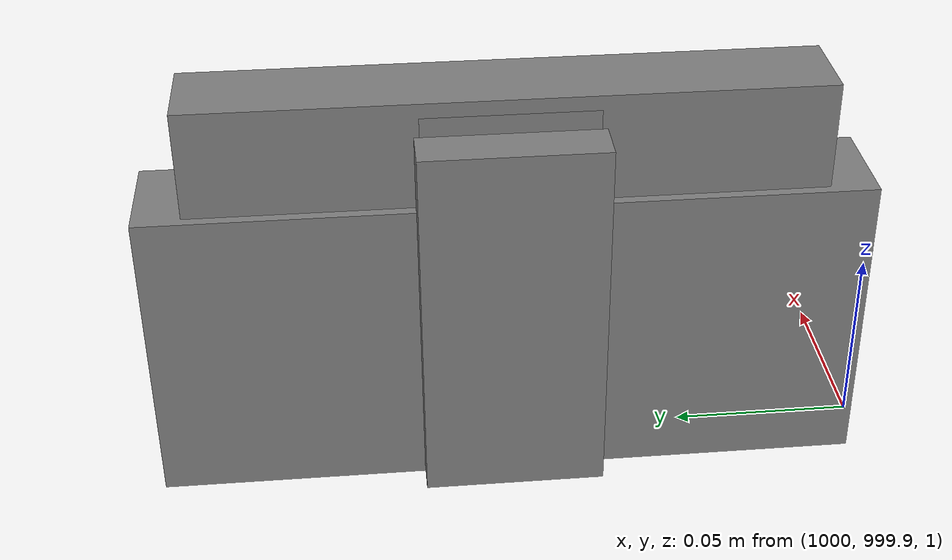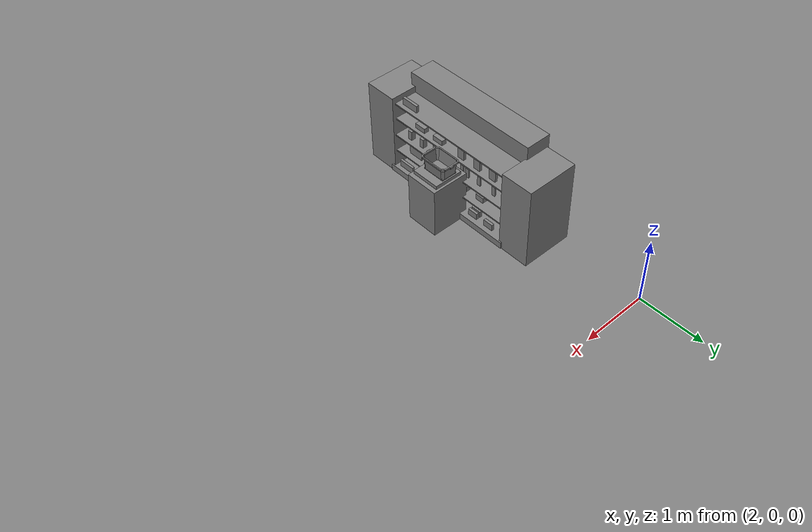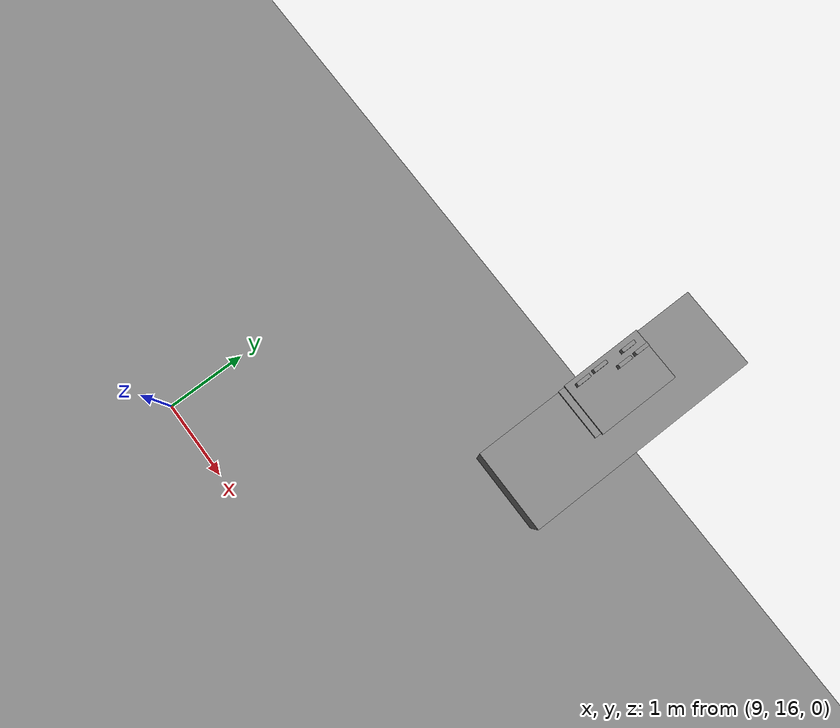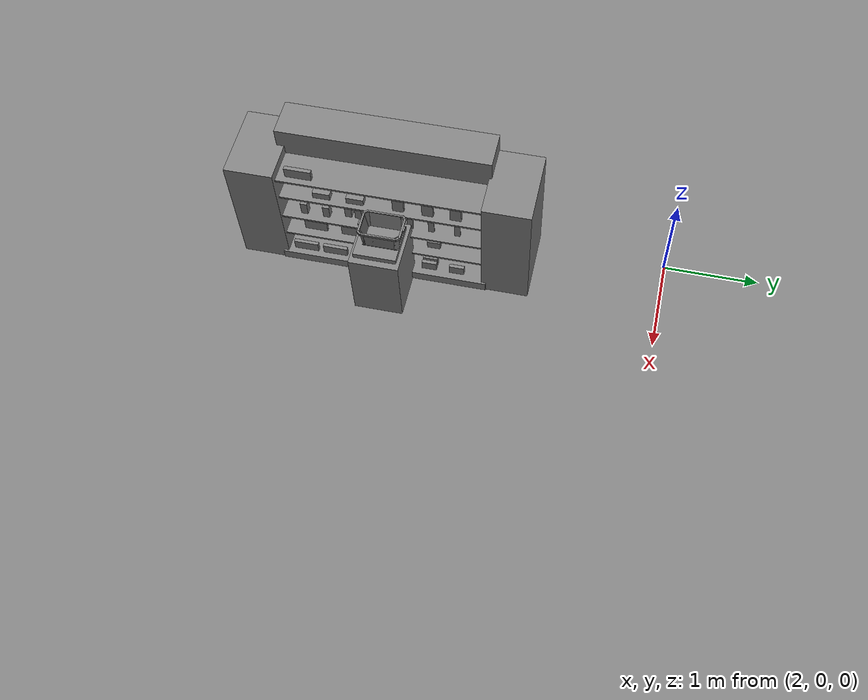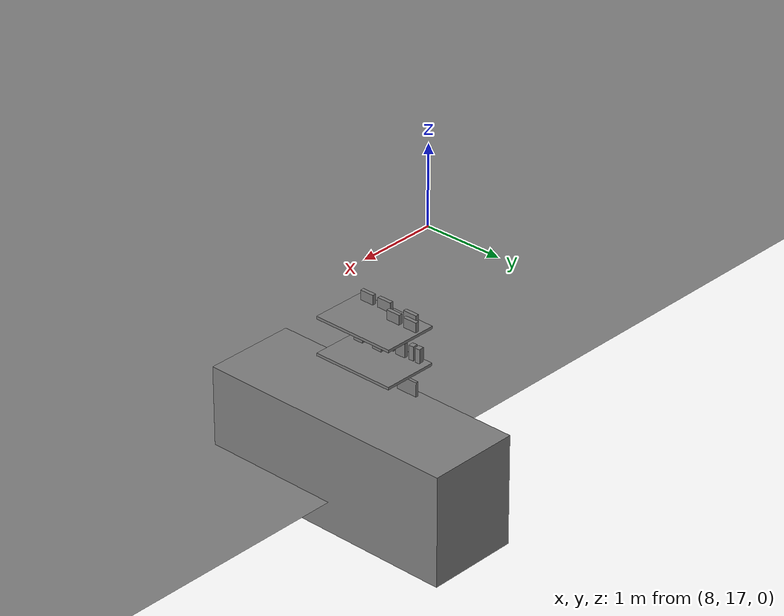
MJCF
<mujoco>
    <option gravity="0.000000000 0.000000000 -9.810000420" timestep="0.0166666" integrator="implicitfast" density="1.225" viscosity="1.8000001e-05" noslip_iterations="10" iterations="100" sdf_iterations="50">
        <flag multiccd="disable"/>
    </option>
    <size memory="1000M"/>
    <compiler coordinate="local"/>
    <worldbody>
        <light cutoff="30" pos="0 1 1" dir="0 -1 -2"/>
        <light cutoff="30" pos="0 -1 1" dir="0 1 -2"/>
        <body pos="2.497505903 -3.185120821 0.763295174" euler="0.000000000 0.000000000 0.000000000" name="openloong_gripper_2f85_fix_base_usda_jiazi_02_e_medicine_03_d">
            <geom contype="1" conaffinity="1" density="1000" type="box" material="" rgba="0.500000000 0.500000000 0.500000000 1.000000000" solimp="0.899999976 0.949999988 0.001000000" friction="1.000000000 0.005000000 0.000100000" solref="0.020000000 1.000000000" margin="0" condim="3" group="0" pos="0.000000000 0.000000000 0.000000000" quat="1.000000000 0.000000000 0.000000000 0.000000000" size="0.035000000 0.035000000 0.071999997" name="openloong_gripper_2f85_fix_base_usda_jiazi_02_e_medicine_03_d_BBD4B609_ED19_43DC_B61A_737F0474112A"/>
            <freejoint name="openloong_gripper_2f85_fix_base_usda_jiazi_02_e_medicine_03_d"/>
        </body>
        <body pos="2.859023094 -2.828485012 0.874997377" euler="89.999946594 0.000000000 0.000000000" name="openloong_gripper_2f85_fix_base_usda_MedicineChest">
            <geom contype="1" conaffinity="1" density="100000" type="box" material="" rgba="0.500000000 0.500000000 0.500000000 1.000000000" solimp="0.899999976 0.949999988 0.001000000" friction="1.000000000 0.899999976 0.000100000" solref="0.020000000 1.000000000" margin="0" condim="3" group="0" pos="-0.132964611 0.198016286 0.194559574" quat="0.359685898 -0.000000596 -0.933073401 0.000003695" size="0.010000000 0.012000000 0.026000001" name="openloong_gripper_2f85_fix_base_usda_geom_DFA438F1_E678_4537_A5FB_E99BCDA76A62"/>
            <geom contype="1" conaffinity="1" density="100000" type="box" material="" rgba="0.500000000 0.500000000 0.500000000 1.000000000" solimp="0.899999976 0.949999988 0.001000000" friction="1.000000000 0.899999976 0.000100000" solref="0.020000000 1.000000000" margin="0" condim="3" group="0" pos="0.000526667 0.104760587 -0.187798262" quat="0.705659389 -0.045368463 0.705640316 -0.045367181" size="0.003000000 0.100000001 0.100000001" name="openloong_gripper_2f85_fix_base_usda_geom_6C777A9B_7426_47A0_B92A_285F4B52CDAC"/>
            <geom contype="1" conaffinity="1" density="100000" type="box" material="" rgba="0.500000000 0.500000000 0.500000000 1.000000000" solimp="0.899999976 0.949999988 0.001000000" friction="1.000000000 0.899999976 0.000100000" solref="0.020000000 1.000000000" margin="0" condim="3" group="0" pos="-0.000797749 0.196027160 -0.223680258" quat="0.707158327 -0.000001520 0.707055092 -0.000001520" size="0.010000000 0.012000000 0.029999999" name="openloong_gripper_2f85_fix_base_usda_geom_80046618_0F33_419F_83F6_9F7E89987DD3"/>
            <geom contype="1" conaffinity="1" density="100000" type="box" material="" rgba="0.500000000 0.500000000 0.500000000 1.000000000" solimp="0.899999976 0.949999988 0.001000000" friction="1.000000000 0.899999976 0.000100000" solref="0.020000000 1.000000000" margin="0" condim="3" group="0" pos="0.000000000 0.005823255 0.000000000" quat="1.000000000 0.000000000 0.000000000 0.000000000" size="0.122000001 0.006000000 0.180000007" name="openloong_gripper_2f85_fix_base_usda_geom_C4F8EEBE_4A74_4E82_8B2F_6891D33D9735"/>
            <geom contype="1" conaffinity="1" density="100000" type="box" material="" rgba="0.500000000 0.500000000 0.500000000 1.000000000" solimp="0.899999976 0.949999988 0.001000000" friction="1.000000000 0.899999976 0.000100000" solref="0.020000000 1.000000000" margin="0" condim="3" group="0" pos="0.000516415 0.102862239 0.189926386" quat="0.705658197 0.045368552 0.705641508 0.045367509" size="0.003000000 0.100000001 0.100000001" name="openloong_gripper_2f85_fix_base_usda_geom_E6F2720C_CCB4_4A19_BF63_0A4171928170"/>
            <geom contype="1" conaffinity="1" density="100000" type="box" material="" rgba="0.500000000 0.500000000 0.500000000 1.000000000" solimp="0.899999976 0.949999988 0.001000000" friction="1.000000000 0.899999976 0.000100000" solref="0.020000000 1.000000000" margin="0" condim="3" group="0" pos="-0.113059282 0.107842624 0.177997828" quat="0.369108677 0.045244619 -0.928185225 -0.013556212" size="0.003000000 0.100000001 0.026000001" name="openloong_gripper_2f85_fix_base_usda_geom_452EFE87_14B9_4723_A996_F43197BC5F98"/>
            <geom contype="1" conaffinity="1" density="100000" type="box" material="" rgba="0.500000000 0.500000000 0.500000000 1.000000000" solimp="0.899999976 0.949999988 0.001000000" friction="1.000000000 0.899999976 0.000100000" solref="0.020000000 1.000000000" margin="0" condim="3" group="0" pos="-0.000797749 0.196027160 0.223680258" quat="0.707158327 -0.000001520 0.707055092 -0.000001520" size="0.010000000 0.012000000 0.029999999" name="openloong_gripper_2f85_fix_base_usda_geom_B9B00299_B5F2_4EE0_8EEC_DA0DA935F7F5"/>
            <geom contype="1" conaffinity="1" density="100000" type="box" material="" rgba="0.500000000 0.500000000 0.500000000 1.000000000" solimp="0.899999976 0.949999988 0.001000000" friction="1.000000000 0.899999976 0.000100000" solref="0.020000000 1.000000000" margin="0" condim="3" group="0" pos="0.128487587 0.105749547 0.000000238" quat="0.999090791 0.000000030 -0.000000002 -0.042632505" size="0.003000000 0.100000001 0.159999996" name="openloong_gripper_2f85_fix_base_usda_geom_A0F0D801_B7B6_4002_84C7_25B6BF27A9DF"/>
            <geom contype="1" conaffinity="1" density="100000" type="box" material="" rgba="0.500000000 0.500000000 0.500000000 1.000000000" solimp="0.899999976 0.949999988 0.001000000" friction="1.000000000 0.899999976 0.000100000" solref="0.020000000 1.000000000" margin="0" condim="3" group="0" pos="-0.116801500 0.106451452 -0.175024986" quat="-0.356188178 0.039200634 -0.932773709 0.039071620" size="0.003000000 0.100000001 0.026000001" name="openloong_gripper_2f85_fix_base_usda_geom_1F5C7E33_3CF2_4069_9AEE_CAF5B3ACC30D"/>
            <geom contype="1" conaffinity="1" density="100000" type="box" material="" rgba="0.500000000 0.500000000 0.500000000 1.000000000" solimp="0.899999976 0.949999988 0.001000000" friction="1.000000000 0.899999976 0.000100000" solref="0.020000000 1.000000000" margin="0" condim="3" group="0" pos="0.000000715 0.198014379 0.208025932" quat="0.707159519 -0.000000089 0.707053959 -0.000000060" size="0.010000000 0.012000000 0.119999997" name="openloong_gripper_2f85_fix_base_usda_geom_AD84267C_1374_4901_8CE0_80258A7AE422"/>
            <geom contype="1" conaffinity="1" density="100000" type="box" material="" rgba="0.500000000 0.500000000 0.500000000 1.000000000" solimp="0.899999976 0.949999988 0.001000000" friction="1.000000000 0.899999976 0.000100000" solref="0.020000000 1.000000000" margin="0" condim="3" group="0" pos="-0.133216143 0.198014021 -0.194619179" quat="-0.359760642 0.000001267 -0.933044553 0.000001341" size="0.010000000 0.012000000 0.026000001" name="openloong_gripper_2f85_fix_base_usda_geom_8383FEE9_8600_419C_9436_E70BBB37B535"/>
            <geom contype="1" conaffinity="1" density="100000" type="box" material="" rgba="0.500000000 0.500000000 0.500000000 1.000000000" solimp="0.899999976 0.949999988 0.001000000" friction="1.000000000 0.899999976 0.000100000" solref="0.020000000 1.000000000" margin="0" condim="3" group="0" pos="0.115026236 0.107592762 0.174144983" quat="0.930772185 0.025311798 -0.363503337 -0.029796928" size="0.003000000 0.100000001 0.026000001" name="openloong_gripper_2f85_fix_base_usda_geom_20CDFCED_C5BB_4774_A3CA_4056ACDE4F55"/>
            <geom contype="1" conaffinity="1" density="100000" type="box" material="" rgba="0.500000000 0.500000000 0.500000000 1.000000000" solimp="0.899999976 0.949999988 0.001000000" friction="1.000000000 0.899999976 0.000100000" solref="0.020000000 1.000000000" margin="0" condim="3" group="0" pos="0.131582499 0.198014021 -0.194822311" quat="0.359707981 -0.000000596 -0.933064938 0.000003695" size="0.010000000 0.012000000 0.026000001" name="openloong_gripper_2f85_fix_base_usda_geom_6178CC78_26F9_44C5_8F42_F4CC1FC5ACB2"/>
            <geom contype="1" conaffinity="1" density="100000" type="box" material="" rgba="0.500000000 0.500000000 0.500000000 1.000000000" solimp="0.899999976 0.949999988 0.001000000" friction="1.000000000 0.899999976 0.000100000" solref="0.020000000 1.000000000" margin="0" condim="3" group="0" pos="0.115736485 0.109648407 -0.172922373" quat="-0.356657803 0.026131347 0.933247149 -0.034088194" size="0.003000000 0.100000001 0.026000001" name="openloong_gripper_2f85_fix_base_usda_geom_660ACD64_4053_4D01_8477_636C66BFD68D"/>
            <geom contype="1" conaffinity="1" density="100000" type="box" material="" rgba="0.500000000 0.500000000 0.500000000 1.000000000" solimp="0.899999976 0.949999988 0.001000000" friction="1.000000000 0.899999976 0.000100000" solref="0.020000000 1.000000000" margin="0" condim="3" group="0" pos="0.145289421 0.198014736 -0.000000238" quat="1.000000000 0.000000000 0.000000000 0.000000000" size="0.009000000 0.012000000 0.180000007" name="openloong_gripper_2f85_fix_base_usda_geom_11D5883E_5589_4C78_97F8_EB63C68B3E8F"/>
            <geom contype="1" conaffinity="1" density="100000" type="box" material="" rgba="0.500000000 0.500000000 0.500000000 1.000000000" solimp="0.899999976 0.949999988 0.001000000" friction="1.000000000 0.899999976 0.000100000" solref="0.020000000 1.000000000" margin="0" condim="3" group="0" pos="0.000000715 0.198014379 -0.208025932" quat="0.707159519 -0.000000089 0.707053959 -0.000000060" size="0.010000000 0.012000000 0.119999997" name="openloong_gripper_2f85_fix_base_usda_geom_D7711915_E724_4AFA_9F03_4B1712D1F007"/>
            <geom contype="1" conaffinity="1" density="100000" type="box" material="" rgba="0.500000000 0.500000000 0.500000000 1.000000000" solimp="0.899999976 0.949999988 0.001000000" friction="1.000000000 0.899999976 0.000100000" solref="0.020000000 1.000000000" margin="0" condim="3" group="0" pos="-0.128487349 0.105749547 0.000000238" quat="0.999090791 0.000000030 -0.000000002 0.042632505" size="0.003000000 0.100000001 0.159999996" name="openloong_gripper_2f85_fix_base_usda_geom_85AE11DE_7894_4CCD_AD87_33A8E54D9D46"/>
            <geom contype="1" conaffinity="1" density="100000" type="box" material="" rgba="0.500000000 0.500000000 0.500000000 1.000000000" solimp="0.899999976 0.949999988 0.001000000" friction="1.000000000 0.899999976 0.000100000" solref="0.020000000 1.000000000" margin="0" condim="3" group="0" pos="-0.145288944 0.198014736 -0.000000238" quat="1.000000000 0.000000000 0.000000000 0.000000000" size="0.009000000 0.012000000 0.180000007" name="openloong_gripper_2f85_fix_base_usda_geom_EAF1AA58_8794_4C8A_8155_A35FB46AEB16"/>
            <geom contype="1" conaffinity="1" density="100000" type="box" material="" rgba="0.500000000 0.500000000 0.500000000 1.000000000" solimp="0.899999976 0.949999988 0.001000000" friction="1.000000000 0.899999976 0.000100000" solref="0.020000000 1.000000000" margin="0" condim="3" group="0" pos="0.132833242 0.198015213 0.194798470" quat="-0.359736264 0.000001252 -0.933053970 0.000001401" size="0.010000000 0.012000000 0.026000001" name="openloong_gripper_2f85_fix_base_usda_geom_25A16A36_C2C6_48FB_A8F6_25FD15FA5A3E"/>
            <freejoint name="openloong_gripper_2f85_fix_base_usda_MedicineChest_joint"/>
            <site size="0.005000000 0.005000000 0.005000000" rgba="0.500000000 0.500000000 0.500000000 1.000000000" pos="0.000000000 0.000000000 0.000000000" quat="1.000000000 0.000000000 0.000000000 0.000000000" group="0" type="sphere" name="openloong_gripper_2f85_fix_base_usda_MedicineChestsite"/>
        </body>
        <body pos="11.742162704 19.970987320 1.373408437" euler="0.000000000 0.000000000 -85.008651733" name="openloong_gripper_2f85_fix_base_usda_jiazi_02_e_medicine_11_pz_b">
            <geom contype="1" conaffinity="1" density="1000" type="box" material="" rgba="0.500000000 0.500000000 0.500000000 1.000000000" solimp="0.899999976 0.949999988 0.001000000" friction="1.000000000 0.005000000 0.000100000" solref="0.020000000 1.000000000" margin="0" condim="3" group="0" pos="0.000000000 0.000000000 0.000000000" quat="1.000000000 0.000000000 0.000000000 0.000000000" size="0.028000001 0.029999999 0.077000000" name="openloong_gripper_2f85_fix_base_usda_jiazi_02_e_medicine_11_pz_b_7A269BD8_1BD3_4D05_9D01_7A4170E29F74"/>
            <freejoint name="openloong_gripper_2f85_fix_base_usda_jiazi_02_e_medicine_11_pz_b"/>
        </body>
        <body pos="2.540798664 -3.660816193 0.494465470" euler="0.000000000 0.000000000 0.000000000" name="openloong_gripper_2f85_fix_base_usda_jiazi_02_e_medicine_10_b">
            <geom contype="1" conaffinity="1" density="1000" type="box" material="" rgba="0.500000000 0.500000000 0.500000000 1.000000000" solimp="0.899999976 0.949999988 0.001000000" friction="1.000000000 0.005000000 0.000100000" solref="0.020000000 1.000000000" margin="0" condim="3" group="0" pos="0.000000000 0.000000000 0.000000000" quat="1.000000000 0.000000000 0.000000000 0.000000000" size="0.015000000 0.119999997 0.079000004" name="openloong_gripper_2f85_fix_base_usda_jiazi_02_e_medicine_10_b_20B30A9F_02F7_41FB_96C8_A6C9330D1143"/>
            <freejoint name="openloong_gripper_2f85_fix_base_usda_jiazi_02_e_medicine_10_b"/>
        </body>
        <body pos="2.540974617 -2.142210245 0.767729700" euler="0.000000000 0.000000000 0.000000000" name="openloong_gripper_2f85_fix_base_usda_jiazi_02_e_medicine_08_d">
            <geom contype="1" conaffinity="1" density="1000" type="box" material="" rgba="0.500000000 0.500000000 0.500000000 1.000000000" solimp="0.899999976 0.949999988 0.001000000" friction="1.000000000 0.005000000 0.000100000" solref="0.020000000 1.000000000" margin="0" condim="3" group="0" pos="0.000000000 0.000000000 0.000000000" quat="1.000000000 0.000000000 0.000000000 0.000000000" size="0.010000000 0.029999999 0.075999998" name="openloong_gripper_2f85_fix_base_usda_jiazi_02_e_medicine_08_d_1E9388FA_CAB6_48AA_9440_758C562A3455"/>
            <freejoint name="openloong_gripper_2f85_fix_base_usda_jiazi_02_e_medicine_08_d"/>
        </body>
        <body pos="2.617633820 -3.462228775 0.195964247" euler="0.000000000 0.000000000 0.000000000" name="openloong_gripper_2f85_fix_base_usda_jiazi_02_e_medicine_17_a">
            <geom contype="1" conaffinity="1" density="1000" type="box" material="" rgba="0.500000000 0.500000000 0.500000000 1.000000000" solimp="0.899999976 0.949999988 0.001000000" friction="1.000000000 0.005000000 0.000100000" solref="0.020000000 1.000000000" margin="0" condim="3" group="0" pos="0.000000000 0.000000000 0.000000000" quat="1.000000000 0.000000000 0.000000000 0.000000000" size="0.018999999 0.129999995 0.056000002" name="openloong_gripper_2f85_fix_base_usda_jiazi_02_e_medicine_17_a_D716A51D_3621_47A3_8380_ACA60E20DC21"/>
            <freejoint name="openloong_gripper_2f85_fix_base_usda_jiazi_02_e_medicine_17_a"/>
        </body>
        <body pos="11.835501671 19.865364075 1.405766487" euler="0.000000000 0.000000000 0.000000000" name="openloong_gripper_2f85_fix_base_usda_jiazi_02_e_medicine_11_f">
            <geom contype="1" conaffinity="1" density="1000" type="box" material="" rgba="0.500000000 0.500000000 0.500000000 1.000000000" solimp="0.899999976 0.949999988 0.001000000" friction="1.000000000 0.005000000 0.000100000" solref="0.020000000 1.000000000" margin="0" condim="3" group="0" pos="0.000000000 0.000000000 0.000000000" quat="1.000000000 0.000000000 0.000000000 0.000000000" size="0.020000000 0.057999998 0.112999998" name="openloong_gripper_2f85_fix_base_usda_jiazi_02_e_medicine_11_f_9000291E_8ED2_42AB_B0C8_89BA30E4D781"/>
            <freejoint name="openloong_gripper_2f85_fix_base_usda_jiazi_02_e_medicine_11_f"/>
        </body>
        <body pos="2.617633820 -3.779438972 0.195964247" euler="0.000000000 0.000000000 0.000000000" name="openloong_gripper_2f85_fix_base_usda_jiazi_02_e_medicine_17_b">
            <geom contype="1" conaffinity="1" density="1000" type="box" material="" rgba="0.500000000 0.500000000 0.500000000 1.000000000" solimp="0.899999976 0.949999988 0.001000000" friction="1.000000000 0.005000000 0.000100000" solref="0.020000000 1.000000000" margin="0" condim="3" group="0" pos="0.000000000 0.000000000 0.000000000" quat="1.000000000 0.000000000 0.000000000 0.000000000" size="0.018999999 0.129999995 0.056000002" name="openloong_gripper_2f85_fix_base_usda_jiazi_02_e_medicine_17_b_6468718D_E42A_407E_8A6D_A3CE143781E6"/>
            <freejoint name="openloong_gripper_2f85_fix_base_usda_jiazi_02_e_medicine_17_b"/>
        </body>
        <body pos="11.758296013 20.215833664 1.746467471" euler="180.000000000 0.000000000 0.000000000" name="openloong_gripper_2f85_fix_base_usda_jiazi_02_e_medicine_16_e">
            <geom contype="1" conaffinity="1" density="1000" type="box" material="" rgba="0.500000000 0.500000000 0.500000000 1.000000000" solimp="0.899999976 0.949999988 0.001000000" friction="1.000000000 0.005000000 0.000100000" solref="0.020000000 1.000000000" margin="0" condim="3" group="0" pos="0.000000000 0.000000000 0.000000000" quat="0.000000000 1.000000000 0.000000000 0.000000000" size="0.020000000 0.079000004 0.052999999" name="openloong_gripper_2f85_fix_base_usda_jiazi_02_e_medicine_16_e_1EA98678_65F3_4A4B_8DB0_AA6D48C6C07F"/>
            <freejoint name="openloong_gripper_2f85_fix_base_usda_jiazi_02_e_medicine_16_e"/>
        </body>
        <body pos="2.527985811 -2.715100288 0.458167851" euler="0.000000000 0.000000000 0.000000000" name="openloong_gripper_2f85_fix_base_usda_jiazi_02_e_medicine_13_a">
            <geom contype="1" conaffinity="1" density="1000" type="box" material="" rgba="0.500000000 0.500000000 0.500000000 1.000000000" solimp="0.899999976 0.949999988 0.001000000" friction="1.000000000 0.005000000 0.000100000" solref="0.020000000 1.000000000" margin="0" condim="3" group="0" pos="0.000000000 0.000000000 0.000000000" quat="1.000000000 0.000000000 0.000000000 0.000000000" size="0.067000002 0.068000004 0.044000000" name="openloong_gripper_2f85_fix_base_usda_jiazi_02_e_medicine_13_a_943C73FC_3AC3_44D5_8D17_7C2D0248B7E0"/>
            <freejoint name="openloong_gripper_2f85_fix_base_usda_jiazi_02_e_medicine_13_a"/>
        </body>
        <body pos="2.557055712 -3.127499342 0.195964247" euler="0.000000000 0.000000000 0.000000000" name="openloong_gripper_2f85_fix_base_usda_jiazi_02_e_medicine_17_c">
            <geom contype="1" conaffinity="1" density="1000" type="box" material="" rgba="0.500000000 0.500000000 0.500000000 1.000000000" solimp="0.899999976 0.949999988 0.001000000" friction="1.000000000 0.005000000 0.000100000" solref="0.020000000 1.000000000" margin="0" condim="3" group="0" pos="0.000000000 0.000000000 0.000000000" quat="1.000000000 0.000000000 0.000000000 0.000000000" size="0.018999999 0.129999995 0.056000002" name="openloong_gripper_2f85_fix_base_usda_jiazi_02_e_medicine_17_c_775D1A4B_8F73_42D5_A040_5770B94E08B7"/>
            <freejoint name="openloong_gripper_2f85_fix_base_usda_jiazi_02_e_medicine_17_c"/>
        </body>
        <body pos="2.555686235 -2.149417400 1.079351544" euler="0.000000000 0.000000000 0.000000000" name="openloong_gripper_2f85_fix_base_usda_jiazi_02_e_medicine_11_b">
            <geom contype="1" conaffinity="1" density="1000" type="box" material="" rgba="0.500000000 0.500000000 0.500000000 1.000000000" solimp="0.899999976 0.949999988 0.001000000" friction="1.000000000 0.005000000 0.000100000" solref="0.020000000 1.000000000" margin="0" condim="3" group="0" pos="0.000000000 0.000000000 0.000000000" quat="1.000000000 0.000000000 0.000000000 0.000000000" size="0.020000000 0.057999998 0.112999998" name="openloong_gripper_2f85_fix_base_usda_jiazi_02_e_medicine_11_b_2DE649CE_FAF0_43BA_A0B4_465790F969BA"/>
            <freejoint name="openloong_gripper_2f85_fix_base_usda_jiazi_02_e_medicine_11_b"/>
        </body>
        <body pos="2.540974617 -2.413386345 0.767729700" euler="0.000000000 0.000000000 0.000000000" name="openloong_gripper_2f85_fix_base_usda_jiazi_02_e_medicine_08_c">
            <geom contype="1" conaffinity="1" density="1000" type="box" material="" rgba="0.500000000 0.500000000 0.500000000 1.000000000" solimp="0.899999976 0.949999988 0.001000000" friction="1.000000000 0.005000000 0.000100000" solref="0.020000000 1.000000000" margin="0" condim="3" group="0" pos="0.000000000 0.000000000 0.000000000" quat="1.000000000 0.000000000 0.000000000 0.000000000" size="0.010000000 0.029999999 0.075999998" name="openloong_gripper_2f85_fix_base_usda_jiazi_02_e_medicine_08_c_FB988349_24E7_4DCF_92FB_BFBA9A56DDEE"/>
            <freejoint name="openloong_gripper_2f85_fix_base_usda_jiazi_02_e_medicine_08_c"/>
        </body>
        <body pos="2.546508551 -2.439894676 0.193254441" euler="0.000000000 0.000000000 0.000000000" name="openloong_gripper_2f85_fix_base_usda_jiazi_02_e_medicine_16_a">
            <geom contype="1" conaffinity="1" density="1000" type="box" material="" rgba="0.500000000 0.500000000 0.500000000 1.000000000" solimp="0.899999976 0.949999988 0.001000000" friction="1.000000000 0.005000000 0.000100000" solref="0.020000000 1.000000000" margin="0" condim="3" group="0" pos="0.000000000 0.000000000 0.000000000" quat="1.000000000 0.000000000 0.000000000 0.000000000" size="0.020000000 0.079000004 0.052999999" name="openloong_gripper_2f85_fix_base_usda_jiazi_02_e_medicine_16_a_8211950E_FCA1_4875_96CB_94BF112D5009"/>
            <freejoint name="openloong_gripper_2f85_fix_base_usda_jiazi_02_e_medicine_16_a"/>
        </body>
        <body pos="2.540974617 -2.634179592 0.767729700" euler="0.000000000 0.000000000 0.000000000" name="openloong_gripper_2f85_fix_base_usda_jiazi_02_e_medicine_08_b">
            <geom contype="1" conaffinity="1" density="1000" type="box" material="" rgba="0.500000000 0.500000000 0.500000000 1.000000000" solimp="0.899999976 0.949999988 0.001000000" friction="1.000000000 0.005000000 0.000100000" solref="0.020000000 1.000000000" margin="0" condim="3" group="0" pos="0.000000000 0.000000000 0.000000000" quat="1.000000000 0.000000000 0.000000000 0.000000000" size="0.010000000 0.029999999 0.075999998" name="openloong_gripper_2f85_fix_base_usda_jiazi_02_e_medicine_08_b_EE267701_3FA6_4A9F_96D3_D946FEBE3DBA"/>
            <freejoint name="openloong_gripper_2f85_fix_base_usda_jiazi_02_e_medicine_08_b"/>
        </body>
        <body pos="0.000000000 0.000000000 0.000000000" euler="0.000000000 0.000000000 0.000000000" name="Static Objcets_Static Objcets">
            <geom contype="1" conaffinity="1" density="1000" type="box" material="" rgba="0.500000000 0.500000000 0.500000000 1.000000000" solimp="0.899999976 0.959999979 0.001000000" friction="1.000000000 0.005000000 0.000100000" solref="0.020000000 1.000000000" margin="0" condim="3" group="0" pos="2.433294058 -2.920555353 0.961130261" quat="1.000000000 0.000000000 0.000000000 0.000000000" size="0.200000003 1.100000024 0.010000000" name="Static Objcets_SM_jiazi_02_e_240DD78D_2919_4968_85A3_549B0B67933B"/>
            <geom contype="1" conaffinity="1" density="1000" type="box" material="" rgba="0.500000000 0.500000000 0.500000000 1.000000000" solimp="0.899999976 0.949999988 0.001000000" friction="1.000000000 0.005000000 0.000100000" solref="0.020000000 1.000000000" margin="0" condim="3" group="0" pos="2.064697266 -2.945113420 0.768164337" quat="1.000000000 0.000000000 0.000000000 0.000000000" size="0.200000003 1.100000024 0.750000000" name="Static Objcets_SM_jiazi_02_c_5210888A_5FDA_46A5_ACB2_B66EEE6E13D6"/>
            <geom contype="1" conaffinity="1" density="1000" type="box" material="" rgba="0.500000000 0.500000000 0.500000000 1.000000000" solimp="0.899999976 0.949999988 0.001000000" friction="1.000000000 0.005000000 0.000100000" solref="0.020000000 1.000000000" margin="0" condim="3" group="0" pos="2.285422325 -1.621193886 0.671916366" quat="1.000000000 0.000000000 0.000000000 0.000000000" size="0.400000006 0.250000000 0.649999976" name="Static Objcets_SM_jiazi_02_a_D7369CF7_E9AE_445D_8C60_AD95F0B27F32"/>
            <geom contype="1" conaffinity="1" density="1000" type="box" material="" rgba="0.500000000 0.500000000 0.500000000 1.000000000" solimp="0.899999976 0.959999979 0.001000000" friction="1.000000000 0.005000000 0.000100000" solref="0.020000000 1.000000000" margin="0" condim="3" group="0" pos="2.506457806 -2.919259548 0.097404450" quat="1.000000000 0.000000000 0.000000000 0.000000000" size="0.200000003 1.100000024 0.050000001" name="Static Objcets_SM_jiazi_02_h_EC5508BB_9DA9_492F_87F4_A35D4FB91737"/>
            <geom contype="1" conaffinity="1" density="1000" type="box" material="" rgba="0.500000000 0.500000000 0.500000000 1.000000000" solimp="0.899999976 0.949999988 0.001000000" friction="1.000000000 0.005000000 0.000100000" solref="0.020000000 1.000000000" margin="0" condim="3" group="0" pos="2.285422325 -4.217127323 0.670601368" quat="1.000000000 0.000000000 0.000000000 0.000000000" size="0.400000006 0.250000000 0.649999976" name="Static Objcets_SM_jiazi_02_b_538A53C1_260A_474A_B0CA_D909F00A264D"/>
            <geom contype="1" conaffinity="1" density="1000" type="box" material="" rgba="0.500000000 0.500000000 0.500000000 1.000000000" solimp="0.899999976 0.959999979 0.001000000" friction="1.000000000 0.005000000 0.000100000" solref="0.020000000 1.000000000" margin="0" condim="3" group="0" pos="2.452836037 -2.920555353 0.682593882" quat="1.000000000 0.000000000 0.000000000 0.000000000" size="0.200000003 1.100000024 0.010000000" name="Static Objcets_SM_jiazi_02_f_C1D87E6E_7033_4350_B803_F4925846B3AF"/>
            <geom contype="1" conaffinity="1" density="1000" type="box" material="" rgba="0.500000000 0.500000000 0.500000000 1.000000000" solimp="0.899999976 0.959999979 0.001000000" friction="1.000000000 0.005000000 0.000100000" solref="0.020000000 1.000000000" margin="0" condim="3" group="0" pos="2.437276840 -2.920555353 1.214537978" quat="1.000000000 0.000000000 0.000000000 0.000000000" size="0.200000003 1.100000024 0.010000000" name="Static Objcets_SM_jiazi_02_d_4B7CC85B_E5F0_4C3F_9A26_CE5141CDFFD1"/>
            <geom contype="1" conaffinity="1" density="1000" type="box" material="" rgba="0.500000000 0.500000000 0.500000000 1.000000000" solimp="0.899999976 0.959999979 0.001000000" friction="1.000000000 0.005000000 0.000100000" solref="0.020000000 1.000000000" margin="0" condim="3" group="0" pos="2.448674917 -2.920555353 0.406362146" quat="1.000000000 0.000000000 0.000000000 0.000000000" size="0.200000003 1.100000024 0.010000000" name="Static Objcets_SM_jiazi_02_g_DB27993E_88D7_443F_9045_AB9657356E7C"/>
            <geom contype="1" conaffinity="1" density="1000" type="box" material="" rgba="0.500000000 0.500000000 0.500000000 1.000000000" solimp="0.899999976 0.959999979 0.001000000" friction="1.000000000 0.005000000 0.000100000" solref="0.020000000 1.000000000" margin="0" condim="3" group="0" pos="11.976007462 19.950820923 1.679351807" quat="1.000000000 0.000000000 0.000000000 0.000000000" size="0.300000012 0.460000008 0.015000000" name="Static Objcets_SM_guizi_06_c_FED7CA23_A133_4C73_8ACE_F1E2926ED851"/>
            <geom contype="1" conaffinity="1" density="1000" type="box" material="" rgba="0.500000000 0.500000000 0.500000000 1.000000000" solimp="0.899999976 0.959999979 0.001000000" friction="1.000000000 0.005000000 0.000100000" solref="0.020000000 1.000000000" margin="0" condim="3" group="0" pos="12.172613144 19.933198929 0.307627976" quat="1.000000000 0.000000000 0.000000000 0.000000000" size="0.500000000 1.450000048 0.600000024" name="Static Objcets_SM_guizi_06_a_B64B55FC_F5A4_471B_9D44_D2976CBFE131"/>
            <geom contype="1" conaffinity="1" density="1000" type="plane" material="" rgba="0.500000000 0.500000000 0.500000000 1.000000000" solimp="0.899999976 0.949999988 0.001000000" friction="1.000000000 0.005000000 0.000100000" solref="0.020000000 1.000000000" margin="0" condim="3" group="0" pos="0.000000000 0.000000000 0.042896956" quat="1.000000000 0.000000000 0.000000000 0.000000000" size="20.000000000 20.000000000 1.000000000" name="Static Objcets_floor_AD19C0CF_58A0_4529_87CF_D69D74C2B599"/>
            <geom contype="1" conaffinity="1" density="1000" type="box" material="" rgba="0.500000000 0.500000000 0.500000000 1.000000000" solimp="0.899999976 0.959999979 0.001000000" friction="1.000000000 0.005000000 0.000100000" solref="0.020000000 1.000000000" margin="0" condim="3" group="0" pos="11.976007462 19.948400497 1.278063059" quat="1.000000000 0.000000000 0.000000000 0.000000000" size="0.300000012 0.460000008 0.015000000" name="Static Objcets_SM_guizi_06_b_C63DC518_2135_450B_AE76_761C86864DD7"/>
        </body>
        <body pos="0.000000000 0.000000000 0.000000000" euler="0.000000000 0.000000000 0.000000000" name="Interactive Objcets_Interactive Objcets"/>
        <body pos="1000.000000000 1000.000000000 1.000000000" euler="0.000000000 0.000000000 0.000000000" name="openloong_gripper_2f85_fix_base_usda_orangebox">
            <geom contype="1" conaffinity="1" density="1000" type="box" material="" rgba="0.500000000 0.500000000 0.500000000 1.000000000" solimp="0.899999976 0.949999988 0.001000000" friction="1.000000000 0.005000000 0.000100000" solref="0.020000000 1.000000000" margin="0" condim="3" group="0" mass="0.5" pos="0.000000000 0.000000000 0.051213536" quat="1.000000000 0.000000000 0.000000000 0.000000000" size="0.024499999 0.024499999 0.051099997" name="openloong_gripper_2f85_fix_base_usda_jiazi_02_e_medicine_03_a_DF95A752_6479_401C_82DE_DA6808C0DA7F"/>
            <freejoint name="openloong_gripper_2f85_fix_base_usda_orangebox_joint"/>
            <site size="0.005000000 0.005000000 0.005000000" rgba="0.500000000 0.500000000 0.500000000 1.000000000" pos="0.000000000 0.000000000 0.000000000" quat="0.999961913 0.008726535 0.000000000 0.000000000" group="0" type="sphere" name="openloong_gripper_2f85_fix_base_usda_orangeboxsite"/>
        </body>
        <body pos="1000.000000000 1000.000000000 1.000000000" euler="0.000000000 0.000000000 0.000000000" name="openloong_gripper_2f85_fix_base_usda_niuhuangwan">
            <geom contype="1" conaffinity="1" density="1000" type="box" material="" rgba="0.500000000 0.500000000 0.500000000 1.000000000" solimp="0.899999976 0.949999988 0.001000000" friction="1.000000000 0.005000000 0.000100000" solref="0.020000000 1.000000000" margin="0" condim="3" group="0" mass="0.5" pos="0.000000000 0.000000000 0.040254507" quat="1.000000000 0.000000000 0.000000000 0.000000000" size="0.014699999 0.096599996 0.041999999" name="openloong_gripper_2f85_fix_base_usda_niuhuangwan_FA4A2624_38F1_4AEA_801C_C78C9019A7C2"/>
            <freejoint name="openloong_gripper_2f85_fix_base_usda_niuhuangwan_joint"/>
            <site size="0.005000000 0.005000000 0.005000000" rgba="0.500000000 0.500000000 0.500000000 1.000000000" pos="0.000000000 0.000000000 0.000000000" quat="0.999961913 0.008726500 0.000000000 0.000000000" group="0" type="sphere" name="openloong_gripper_2f85_fix_base_usda_niuhuangwansite"/>
        </body>
        <body pos="2.660705090 -2.865085602 1.328035116" euler="-27.397060394 -52.162464142 24.235466003" mocap="true" name="spotlight3_SpotLight"/>
        <body pos="1000.000000000 1000.000000000 1.000000000" euler="0.000000000 0.000000000 0.000000000" name="openloong_gripper_2f85_fix_base_usda_xiaokepian">
            <geom contype="1" conaffinity="1" density="1000" type="box" material="" rgba="0.500000000 0.500000000 0.500000000 1.000000000" solimp="0.899999976 0.949999988 0.001000000" friction="1.000000000 0.005000000 0.000100000" solref="0.020000000 1.000000000" margin="0" condim="3" group="0" mass="0.5" pos="0.000000000 0.000000000 0.055557761" quat="1.000000000 0.000000000 0.000000000 0.000000000" size="0.011900000 0.083999999 0.055999998" name="openloong_gripper_2f85_fix_base_usda_jiazi_02_e_medicine_10_a_853EC348_BF9B_46F5_8FF5_ACB0A6B8FB42"/>
            <freejoint name="openloong_gripper_2f85_fix_base_usda_xiaokepian_joint"/>
            <site size="0.005000000 0.005000000 0.005000000" rgba="0.500000000 0.500000000 0.500000000 1.000000000" pos="0.000000000 0.000000000 0.000000000" quat="0.999961913 0.008726534 0.000000000 0.000000000" group="0" type="sphere" name="openloong_gripper_2f85_fix_base_usda_xiaokepiansite"/>
        </body>
        <body pos="3.030019999 -2.997813940 1.346898079" euler="-59.600761414 2.297869205 -165.848876953" mocap="true" name="spotlight6_SpotLight"/>
        <body pos="2.581751347 -2.455089331 1.469120026" euler="172.340164185 23.372190475 -36.007553101" mocap="true" name="spotlight5_SpotLight"/>
        <body pos="1000.000000000 1000.000000000 1.000000000" euler="0.000000000 0.000000000 0.000000000" name="openloong_gripper_2f85_fix_base_usda_qinghuopian">
            <geom contype="1" conaffinity="1" density="1000" type="box" material="" rgba="0.500000000 0.500000000 0.500000000 1.000000000" solimp="0.899999976 0.949999988 0.001000000" friction="1.000000000 0.005000000 0.000100000" solref="0.020000000 1.000000000" margin="0" condim="3" group="0" mass="0.5" pos="0.000000000 0.000000000 0.036895368" quat="1.000000000 0.000000000 0.000000000 0.000000000" size="0.014000000 0.055300001 0.037099998" name="openloong_gripper_2f85_fix_base_usda_jiazi_02_e_medicine_16_b_A516D1F5_69ED_4600_BE2C_271FB206C33C"/>
            <freejoint name="openloong_gripper_2f85_fix_base_usda_qinghuopian_joint"/>
            <site size="0.005000000 0.005000000 0.005000000" rgba="0.500000000 0.500000000 0.500000000 1.000000000" pos="0.000000000 0.000000000 0.000000000" quat="0.999961913 0.008726534 0.000000000 0.000000000" group="0" type="sphere" name="openloong_gripper_2f85_fix_base_usda_qinghuopiansite"/>
        </body>
        <body pos="1000.000000000 1000.000000000 1.000000000" euler="0.000000000 0.000000000 0.000000000" name="openloong_gripper_2f85_fix_base_usda_pipalu">
            <geom contype="1" conaffinity="1" density="1000" type="box" material="" rgba="0.500000000 0.500000000 0.500000000 1.000000000" solimp="0.899999976 0.949999988 0.001000000" friction="1.000000000 0.005000000 0.000100000" solref="0.020000000 1.000000000" margin="0" condim="3" group="0" mass="0.5" pos="0.000000000 0.000000000 0.053639743" quat="1.000000000 0.000000000 0.000000000 0.000000000" size="0.011900000 0.023100000 0.053900000" name="openloong_gripper_2f85_fix_base_usda_jiazi_02_e_medicine_08_a_BF6E7F6B_5E1B_4D8F_8679_A9104CF04FC0"/>
            <freejoint name="openloong_gripper_2f85_fix_base_usda_pipalu_joint"/>
            <site size="0.005000000 0.005000000 0.005000000" rgba="0.500000000 0.500000000 0.500000000 1.000000000" pos="0.000000000 0.000000000 0.000000000" quat="0.999961913 0.008726534 0.000000000 0.000000000" group="0" type="sphere" name="openloong_gripper_2f85_fix_base_usda_pipalusite"/>
        </body>
        <body pos="2.877940178 -2.751950979 0.062857389" euler="0.000000000 0.000000000 0.000000000" name="[25330601617012]_DeliveryRobot_01">
            <geom contype="1" conaffinity="1" density="1000" type="box" material="" rgba="0.500000000 0.500000000 0.500000000 1.000000000" solimp="0.899999976 0.949999988 0.001000000" friction="1.000000000 0.005000000 0.000100000" solref="0.020000000 1.000000000" margin="0" condim="3" group="0" pos="0.000000000 -0.111846209 0.319800019" quat="1.000000000 0.000000000 0.000000000 0.000000000" size="0.289999992 0.254999995 0.419999987" name="[25330601617012]_geom_19F85526_3EC8_42EA_BBC9_236C26C9ED1A"/>
            <geom contype="1" conaffinity="1" density="1000" type="box" material="" rgba="0.500000000 0.500000000 0.500000000 1.000000000" solimp="0.899999976 0.949999988 0.001000000" friction="1.000000000 0.005000000 0.000100000" solref="0.020000000 1.000000000" margin="0" condim="3" group="0" pos="0.000000000 -0.111846209 0.744405389" quat="1.000000000 0.000000000 0.000000000 0.000000000" size="0.219999999 0.219999999 0.050000001" name="[25330601617012]_geom_0D529B57_BC60_4AB9_B77E_EF57B1FEB766"/>
        </body>
        <body pos="2.497505903 -3.292093039 0.763295174" euler="0.000000000 0.000000000 0.000000000" name="openloong_gripper_2f85_fix_base_usda_jiazi_02_e_medicine_03_c">
            <geom contype="1" conaffinity="1" density="1000" type="box" material="" rgba="0.500000000 0.500000000 0.500000000 1.000000000" solimp="0.899999976 0.949999988 0.001000000" friction="1.000000000 0.005000000 0.000100000" solref="0.020000000 1.000000000" margin="0" condim="3" group="0" pos="0.000000000 0.000000000 0.000000000" quat="1.000000000 0.000000000 0.000000000 0.000000000" size="0.035000000 0.035000000 0.071999997" name="openloong_gripper_2f85_fix_base_usda_jiazi_02_e_medicine_03_c_3CC46D91_8768_4BE7_AF8A_D1F11F9E8BDF"/>
            <freejoint name="openloong_gripper_2f85_fix_base_usda_jiazi_02_e_medicine_03_c"/>
        </body>
        <body pos="11.763878822 20.100526810 1.405766487" euler="0.000000000 0.000000000 0.000000000" name="openloong_gripper_2f85_fix_base_usda_jiazi_02_e_medicine_11_d">
            <geom contype="1" conaffinity="1" density="1000" type="box" material="" rgba="0.500000000 0.500000000 0.500000000 1.000000000" solimp="0.899999976 0.949999988 0.001000000" friction="1.000000000 0.005000000 0.000100000" solref="0.020000000 1.000000000" margin="0" condim="3" group="0" pos="0.000000000 0.000000000 0.000000000" quat="1.000000000 0.000000000 0.000000000 0.000000000" size="0.020000000 0.057999998 0.112999998" name="openloong_gripper_2f85_fix_base_usda_jiazi_02_e_medicine_11_d_65ED713F_5582_4D68_AA18_249B5FB1AB07"/>
            <freejoint name="openloong_gripper_2f85_fix_base_usda_jiazi_02_e_medicine_11_d"/>
        </body>
        <body pos="11.742162704 19.632486343 1.369683743" euler="0.000000000 0.000000000 -85.008651733" name="openloong_gripper_2f85_fix_base_usda_jiazi_02_e_medicine_11_pz_a">
            <geom contype="1" conaffinity="1" density="1000" type="box" material="" rgba="0.500000000 0.500000000 0.500000000 1.000000000" solimp="0.899999976 0.949999988 0.001000000" friction="1.000000000 0.005000000 0.000100000" solref="0.020000000 1.000000000" margin="0" condim="3" group="0" pos="0.000000000 0.000000000 0.000000000" quat="1.000000000 0.000000000 0.000000000 0.000000000" size="0.028000001 0.029999999 0.077000000" name="openloong_gripper_2f85_fix_base_usda_jiazi_02_e_medicine_11_pz_a_52A11CAE_83B2_4F36_A8FE_2EAB7A563F14"/>
            <freejoint name="openloong_gripper_2f85_fix_base_usda_jiazi_02_e_medicine_11_pz_a"/>
        </body>
        <body pos="11.835501671 19.621755600 1.405766487" euler="0.000000000 0.000000000 0.000000000" name="openloong_gripper_2f85_fix_base_usda_jiazi_02_e_medicine_11_g">
            <geom contype="1" conaffinity="1" density="1000" type="box" material="" rgba="0.500000000 0.500000000 0.500000000 1.000000000" solimp="0.899999976 0.949999988 0.001000000" friction="1.000000000 0.005000000 0.000100000" solref="0.020000000 1.000000000" margin="0" condim="3" group="0" pos="0.000000000 0.000000000 0.000000000" quat="1.000000000 0.000000000 0.000000000 0.000000000" size="0.020000000 0.057999998 0.112999998" name="openloong_gripper_2f85_fix_base_usda_jiazi_02_e_medicine_11_g_0FB14D68_F575_44A5_9859_0BB9546E1CB1"/>
            <freejoint name="openloong_gripper_2f85_fix_base_usda_jiazi_02_e_medicine_11_g"/>
        </body>
        <body pos="2.608781099 -2.439894676 0.193254441" euler="0.000000000 0.000000000 0.000000000" name="openloong_gripper_2f85_fix_base_usda_jiazi_02_e_medicine_16_b">
            <geom contype="1" conaffinity="1" density="1000" type="box" material="" rgba="0.500000000 0.500000000 0.500000000 1.000000000" solimp="0.899999976 0.949999988 0.001000000" friction="1.000000000 0.005000000 0.000100000" solref="0.020000000 1.000000000" margin="0" condim="3" group="0" pos="0.000000000 0.000000000 0.000000000" quat="1.000000000 0.000000000 0.000000000 0.000000000" size="0.020000000 0.079000004 0.052999999" name="openloong_gripper_2f85_fix_base_usda_jiazi_02_e_medicine_16_b_F96B863C_F227_47F9_B5C5_CC4E390C9C80"/>
            <freejoint name="openloong_gripper_2f85_fix_base_usda_jiazi_02_e_medicine_16_b"/>
        </body>
        <body pos="2.535823345 -3.535886526 1.006494284" euler="0.000000000 0.000000000 0.000000000" name="openloong_gripper_2f85_fix_base_usda_jiazi_02_e_medicine_01_a">
            <geom contype="1" conaffinity="1" density="1000" type="box" material="" rgba="0.500000000 0.500000000 0.500000000 1.000000000" solimp="0.899999976 0.949999988 0.001000000" friction="1.000000000 0.005000000 0.000100000" solref="0.020000000 1.000000000" margin="0" condim="3" group="0" pos="0.000000000 0.000000000 0.000000000" quat="1.000000000 0.000000000 0.000000000 0.000000000" size="0.039999999 0.090000004 0.039999999" name="openloong_gripper_2f85_fix_base_usda_jiazi_02_e_medicine_01_a_1196CFAA_7727_43B9_B4C5_A935E583A41C"/>
            <freejoint name="openloong_gripper_2f85_fix_base_usda_jiazi_02_e_medicine_01_a"/>
        </body>
        <body pos="2.535823345 -3.186250448 1.006494284" euler="0.000000000 0.000000000 0.000000000" name="openloong_gripper_2f85_fix_base_usda_jiazi_02_e_medicine_01_b">
            <geom contype="1" conaffinity="1" density="1000" type="box" material="" rgba="0.500000000 0.500000000 0.500000000 1.000000000" solimp="0.899999976 0.949999988 0.001000000" friction="1.000000000 0.005000000 0.000100000" solref="0.020000000 1.000000000" margin="0" condim="3" group="0" pos="0.000000000 0.000000000 0.000000000" quat="1.000000000 0.000000000 0.000000000 0.000000000" size="0.039999999 0.090000004 0.039999999" name="openloong_gripper_2f85_fix_base_usda_jiazi_02_e_medicine_01_b_84CB71C4_BC02_4D36_85C1_F30FEA631E8F"/>
            <freejoint name="openloong_gripper_2f85_fix_base_usda_jiazi_02_e_medicine_01_b"/>
        </body>
        <body pos="2.619754076 -2.721762657 0.193254441" euler="0.000000000 0.000000000 0.000000000" name="openloong_gripper_2f85_fix_base_usda_jiazi_02_e_medicine_16_d">
            <geom contype="1" conaffinity="1" density="1000" type="box" material="" rgba="0.500000000 0.500000000 0.500000000 1.000000000" solimp="0.899999976 0.949999988 0.001000000" friction="1.000000000 0.005000000 0.000100000" solref="0.020000000 1.000000000" margin="0" condim="3" group="0" pos="0.000000000 0.000000000 0.000000000" quat="1.000000000 0.000000000 0.000000000 0.000000000" size="0.020000000 0.079000004 0.052999999" name="openloong_gripper_2f85_fix_base_usda_jiazi_02_e_medicine_16_d_E7EEA093_EC05_40E7_90BC_68853613FA86"/>
            <freejoint name="openloong_gripper_2f85_fix_base_usda_jiazi_02_e_medicine_16_d"/>
        </body>
        <body pos="11.742162704 20.304208755 1.369683743" euler="0.000000000 0.000000000 -85.008651733" name="openloong_gripper_2f85_fix_base_usda_jiazi_02_e_medicine_11_pz_c">
            <geom contype="1" conaffinity="1" density="1000" type="box" material="" rgba="0.500000000 0.500000000 0.500000000 1.000000000" solimp="0.899999976 0.949999988 0.001000000" friction="1.000000000 0.005000000 0.000100000" solref="0.020000000 1.000000000" margin="0" condim="3" group="0" pos="0.000000000 0.000000000 0.000000000" quat="1.000000000 0.000000000 0.000000000 0.000000000" size="0.028000001 0.029999999 0.077000000" name="openloong_gripper_2f85_fix_base_usda_jiazi_02_e_medicine_11_pz_c_A948CB17_090B_47D4_884A_F2AC537060BF"/>
            <freejoint name="openloong_gripper_2f85_fix_base_usda_jiazi_02_e_medicine_11_pz_c"/>
        </body>
        <body pos="11.749706268 19.659208298 1.746467471" euler="180.000000000 0.000000000 0.000000000" name="openloong_gripper_2f85_fix_base_usda_jiazi_02_e_medicine_16_g">
            <geom contype="1" conaffinity="1" density="1000" type="box" material="" rgba="0.500000000 0.500000000 0.500000000 1.000000000" solimp="0.899999976 0.949999988 0.001000000" friction="1.000000000 0.005000000 0.000100000" solref="0.020000000 1.000000000" margin="0" condim="3" group="0" pos="0.000000000 0.000000000 0.000000000" quat="0.000000000 1.000000000 0.000000000 0.000000000" size="0.020000000 0.079000004 0.052999999" name="openloong_gripper_2f85_fix_base_usda_jiazi_02_e_medicine_16_g_BF13D290_421F_40D0_A6F6_2926FFE66B3C"/>
            <freejoint name="openloong_gripper_2f85_fix_base_usda_jiazi_02_e_medicine_16_g"/>
        </body>
        <body pos="11.742162704 20.226203918 1.369683743" euler="0.000000000 0.000000000 -85.008651733" name="openloong_gripper_2f85_fix_base_usda_jiazi_02_e_medicine_11_pz_d">
            <geom contype="1" conaffinity="1" density="1000" type="box" material="" rgba="0.500000000 0.500000000 0.500000000 1.000000000" solimp="0.899999976 0.949999988 0.001000000" friction="1.000000000 0.005000000 0.000100000" solref="0.020000000 1.000000000" margin="0" condim="3" group="0" pos="0.000000000 0.000000000 0.000000000" quat="1.000000000 0.000000000 0.000000000 0.000000000" size="0.028000001 0.029999999 0.077000000" name="openloong_gripper_2f85_fix_base_usda_jiazi_02_e_medicine_11_pz_d_92111B7C_EEC9_46DB_8D2A_34F70CA891AF"/>
            <freejoint name="openloong_gripper_2f85_fix_base_usda_jiazi_02_e_medicine_11_pz_d"/>
        </body>
        <body pos="11.751025200 19.770164490 1.405766487" euler="0.000000000 0.000000000 0.000000000" name="openloong_gripper_2f85_fix_base_usda_jiazi_02_e_medicine_11_e">
            <geom contype="1" conaffinity="1" density="1000" type="box" material="" rgba="0.500000000 0.500000000 0.500000000 1.000000000" solimp="0.899999976 0.949999988 0.001000000" friction="1.000000000 0.005000000 0.000100000" solref="0.020000000 1.000000000" margin="0" condim="3" group="0" pos="0.000000000 0.000000000 0.000000000" quat="1.000000000 0.000000000 0.000000000 0.000000000" size="0.020000000 0.057999998 0.112999998" name="openloong_gripper_2f85_fix_base_usda_jiazi_02_e_medicine_11_e_88FDF0A2_6940_4EAB_ABC6_028FDA1BE17C"/>
            <freejoint name="openloong_gripper_2f85_fix_base_usda_jiazi_02_e_medicine_11_e"/>
        </body>
        <body pos="2.608781099 -2.144529104 0.193254441" euler="0.000000000 0.000000000 0.000000000" name="openloong_gripper_2f85_fix_base_usda_jiazi_02_e_medicine_16_c">
            <geom contype="1" conaffinity="1" density="1000" type="box" material="" rgba="0.500000000 0.500000000 0.500000000 1.000000000" solimp="0.899999976 0.949999988 0.001000000" friction="1.000000000 0.005000000 0.000100000" solref="0.020000000 1.000000000" margin="0" condim="3" group="0" pos="0.000000000 0.000000000 0.000000000" quat="1.000000000 0.000000000 0.000000000 0.000000000" size="0.020000000 0.079000004 0.052999999" name="openloong_gripper_2f85_fix_base_usda_jiazi_02_e_medicine_16_c_A7043BB3_1DD8_4825_96CB_BAF07120AE71"/>
            <freejoint name="openloong_gripper_2f85_fix_base_usda_jiazi_02_e_medicine_16_c"/>
        </body>
        <body pos="11.855587959 20.093915939 1.746467471" euler="180.000000000 0.000000000 0.000000000" name="openloong_gripper_2f85_fix_base_usda_jiazi_02_e_medicine_16_i">
            <geom contype="1" conaffinity="1" density="1000" type="box" material="" rgba="0.500000000 0.500000000 0.500000000 1.000000000" solimp="0.899999976 0.949999988 0.001000000" friction="1.000000000 0.005000000 0.000100000" solref="0.020000000 1.000000000" margin="0" condim="3" group="0" pos="0.000000000 0.000000000 0.000000000" quat="0.000000000 1.000000000 0.000000000 0.000000000" size="0.020000000 0.079000004 0.052999999" name="openloong_gripper_2f85_fix_base_usda_jiazi_02_e_medicine_16_i_223BBC35_C4FE_452A_870E_CBC29DFBC8BD"/>
            <freejoint name="openloong_gripper_2f85_fix_base_usda_jiazi_02_e_medicine_16_i"/>
        </body>
        <body pos="2.555686235 -2.437009096 1.079351544" euler="0.000000000 0.000000000 0.000000000" name="openloong_gripper_2f85_fix_base_usda_jiazi_02_e_medicine_11_a">
            <geom contype="1" conaffinity="1" density="1000" type="box" material="" rgba="0.500000000 0.500000000 0.500000000 1.000000000" solimp="0.899999976 0.949999988 0.001000000" friction="1.000000000 0.005000000 0.000100000" solref="0.020000000 1.000000000" margin="0" condim="3" group="0" pos="0.000000000 0.000000000 0.000000000" quat="1.000000000 0.000000000 0.000000000 0.000000000" size="0.020000000 0.057999998 0.112999998" name="openloong_gripper_2f85_fix_base_usda_jiazi_02_e_medicine_11_a_DD840847_F553_4EAE_BBD0_6DC742BFE35F"/>
            <freejoint name="openloong_gripper_2f85_fix_base_usda_jiazi_02_e_medicine_11_a"/>
        </body>
        <body pos="2.543471813 -3.745966911 0.763295174" euler="0.000000000 0.000000000 0.000000000" name="openloong_gripper_2f85_fix_base_usda_jiazi_02_e_medicine_03_a">
            <geom contype="1" conaffinity="1" density="1000" type="box" material="" rgba="0.500000000 0.500000000 0.500000000 1.000000000" solimp="0.899999976 0.949999988 0.001000000" friction="1.000000000 0.005000000 0.000100000" solref="0.020000000 1.000000000" margin="0" condim="3" group="0" pos="0.000000000 0.000000000 0.000000000" quat="1.000000000 0.000000000 0.000000000 0.000000000" size="0.035000000 0.035000000 0.071999997" name="openloong_gripper_2f85_fix_base_usda_jiazi_02_e_medicine_03_a_90986806_69BB_40C9_BAEB_9A4F2D1FD3CE"/>
            <freejoint name="openloong_gripper_2f85_fix_base_usda_jiazi_02_e_medicine_03_a"/>
        </body>
        <body pos="2.543471813 -3.511630297 0.763295174" euler="0.000000000 0.000000000 0.000000000" name="openloong_gripper_2f85_fix_base_usda_jiazi_02_e_medicine_03_b">
            <geom contype="1" conaffinity="1" density="1000" type="box" material="" rgba="0.500000000 0.500000000 0.500000000 1.000000000" solimp="0.899999976 0.949999988 0.001000000" friction="1.000000000 0.005000000 0.000100000" solref="0.020000000 1.000000000" margin="0" condim="3" group="0" pos="0.000000000 0.000000000 0.000000000" quat="1.000000000 0.000000000 0.000000000 0.000000000" size="0.035000000 0.035000000 0.071999997" name="openloong_gripper_2f85_fix_base_usda_jiazi_02_e_medicine_03_b_6225B4E4_53D5_4ECD_AA7A_18D396E5ED19"/>
            <freejoint name="openloong_gripper_2f85_fix_base_usda_jiazi_02_e_medicine_03_b"/>
        </body>
        <body pos="2.555686235 -2.738002539 1.079351544" euler="0.000000000 0.000000000 0.000000000" name="openloong_gripper_2f85_fix_base_usda_jiazi_02_e_medicine_11_c">
            <geom contype="1" conaffinity="1" density="1000" type="box" material="" rgba="0.500000000 0.500000000 0.500000000 1.000000000" solimp="0.899999976 0.949999988 0.001000000" friction="1.000000000 0.005000000 0.000100000" solref="0.020000000 1.000000000" margin="0" condim="3" group="0" pos="0.000000000 0.000000000 0.000000000" quat="1.000000000 0.000000000 0.000000000 0.000000000" size="0.020000000 0.057999998 0.112999998" name="openloong_gripper_2f85_fix_base_usda_jiazi_02_e_medicine_11_c_6CFD8739_313E_406E_B00B_C7BE87E69366"/>
            <freejoint name="openloong_gripper_2f85_fix_base_usda_jiazi_02_e_medicine_11_c"/>
        </body>
        <body pos="2.540974617 -2.737313509 0.767729700" euler="0.000000000 0.000000000 0.000000000" name="openloong_gripper_2f85_fix_base_usda_jiazi_02_e_medicine_08_a">
            <geom contype="1" conaffinity="1" density="1000" type="box" material="" rgba="0.500000000 0.500000000 0.500000000 1.000000000" solimp="0.899999976 0.949999988 0.001000000" friction="1.000000000 0.005000000 0.000100000" solref="0.020000000 1.000000000" margin="0" condim="3" group="0" pos="0.000000000 0.000000000 0.000000000" quat="1.000000000 0.000000000 0.000000000 0.000000000" size="0.010000000 0.029999999 0.075999998" name="openloong_gripper_2f85_fix_base_usda_jiazi_02_e_medicine_08_a_8593FF71_A4F3_40F7_94C0_B4287660BCF8"/>
            <freejoint name="openloong_gripper_2f85_fix_base_usda_jiazi_02_e_medicine_08_a"/>
        </body>
        <body pos="2.547302485 -3.744830847 1.280401945" euler="0.000000000 0.000000000 0.000000000" name="openloong_gripper_2f85_fix_base_usda_jiazi_02_e_medicine_14_b">
            <geom contype="1" conaffinity="1" density="1000" type="box" material="" rgba="0.500000000 0.500000000 0.500000000 1.000000000" solimp="0.899999976 0.949999988 0.001000000" friction="1.000000000 0.005000000 0.000100000" solref="0.020000000 1.000000000" margin="0" condim="3" group="0" pos="0.000000000 0.000000000 0.000000000" quat="1.000000000 0.000000000 0.000000000 0.000000000" size="0.021000000 0.136999995 0.057000000" name="openloong_gripper_2f85_fix_base_usda_jiazi_02_e_medicine_14_b_A8ECE30E_0531_4E64_ADEA_4FFD84B96280"/>
            <freejoint name="openloong_gripper_2f85_fix_base_usda_jiazi_02_e_medicine_14_b"/>
        </body>
        <body pos="11.743835449 19.873136520 1.746467471" euler="180.000000000 0.000000000 0.000000000" name="openloong_gripper_2f85_fix_base_usda_jiazi_02_e_medicine_16_f">
            <geom contype="1" conaffinity="1" density="1000" type="box" material="" rgba="0.500000000 0.500000000 0.500000000 1.000000000" solimp="0.899999976 0.949999988 0.001000000" friction="1.000000000 0.005000000 0.000100000" solref="0.020000000 1.000000000" margin="0" condim="3" group="0" pos="0.000000000 0.000000000 0.000000000" quat="0.000000000 1.000000000 0.000000000 0.000000000" size="0.020000000 0.079000004 0.052999999" name="openloong_gripper_2f85_fix_base_usda_jiazi_02_e_medicine_16_f_9AA530DC_8E79_497D_A30E_76B956FB7C67"/>
            <freejoint name="openloong_gripper_2f85_fix_base_usda_jiazi_02_e_medicine_16_f"/>
        </body>
        <body pos="11.746563911 19.764736176 0.987372577" euler="0.000000000 0.000000000 180.000000000" name="openloong_gripper_2f85_fix_base_usda_jiazi_02_e_medicine_10_d">
            <geom contype="1" conaffinity="1" density="1000" type="box" material="" rgba="0.500000000 0.500000000 0.500000000 1.000000000" solimp="0.899999976 0.949999988 0.001000000" friction="1.000000000 0.005000000 0.000100000" solref="0.020000000 1.000000000" margin="0" condim="3" group="0" pos="0.000000000 0.000000000 0.000000000" quat="0.000000000 0.000000000 0.000000000 -1.000000000" size="0.015000000 0.119999997 0.079000004" name="openloong_gripper_2f85_fix_base_usda_jiazi_02_e_medicine_10_d_95A95FB1_016A_4C63_A704_460C338A902E"/>
            <freejoint name="openloong_gripper_2f85_fix_base_usda_jiazi_02_e_medicine_10_d"/>
        </body>
        <body pos="2.540798664 -3.265180588 0.494465470" euler="0.000000000 0.000000000 0.000000000" name="openloong_gripper_2f85_fix_base_usda_jiazi_02_e_medicine_10_a">
            <geom contype="1" conaffinity="1" density="1000" type="box" material="" rgba="0.500000000 0.500000000 0.500000000 1.000000000" solimp="0.899999976 0.949999988 0.001000000" friction="1.000000000 0.005000000 0.000100000" solref="0.020000000 1.000000000" margin="0" condim="3" group="0" pos="0.000000000 0.000000000 0.000000000" quat="1.000000000 0.000000000 0.000000000 0.000000000" size="0.015000000 0.119999997 0.079000004" name="openloong_gripper_2f85_fix_base_usda_jiazi_02_e_medicine_10_a_78FC03E3_065A_4195_ACA6_197A87A4E770"/>
            <freejoint name="openloong_gripper_2f85_fix_base_usda_jiazi_02_e_medicine_10_a"/>
        </body>
        <body pos="2.478220224 -2.398950338 0.458167851" euler="0.000000000 0.000000000 0.000000000" name="openloong_gripper_2f85_fix_base_usda_jiazi_02_e_medicine_13_b">
            <geom contype="1" conaffinity="1" density="1000" type="box" material="" rgba="0.500000000 0.500000000 0.500000000 1.000000000" solimp="0.899999976 0.949999988 0.001000000" friction="1.000000000 0.005000000 0.000100000" solref="0.020000000 1.000000000" margin="0" condim="3" group="0" pos="0.000000000 0.000000000 0.000000000" quat="1.000000000 0.000000000 0.000000000 0.000000000" size="0.067000002 0.068000004 0.044000000" name="openloong_gripper_2f85_fix_base_usda_jiazi_02_e_medicine_13_b_EF04E552_8193_49D4_ADF6_607DADAD4D85"/>
            <freejoint name="openloong_gripper_2f85_fix_base_usda_jiazi_02_e_medicine_13_b"/>
        </body>
        <body pos="11.751626015 20.166509628 0.987222910" euler="0.000000000 0.000000000 0.000000000" name="openloong_gripper_2f85_fix_base_usda_jiazi_02_e_medicine_10_c">
            <geom contype="1" conaffinity="1" density="1000" type="box" material="" rgba="0.500000000 0.500000000 0.500000000 1.000000000" solimp="0.899999976 0.949999988 0.001000000" friction="1.000000000 0.005000000 0.000100000" solref="0.020000000 1.000000000" margin="0" condim="3" group="0" pos="0.000000000 0.000000000 0.000000000" quat="1.000000000 0.000000000 0.000000000 0.000000000" size="0.015000000 0.119999997 0.079000004" name="openloong_gripper_2f85_fix_base_usda_jiazi_02_e_medicine_10_c_97C830B5_52A0_4375_9C19_0EA1BEBBDC22"/>
            <freejoint name="openloong_gripper_2f85_fix_base_usda_jiazi_02_e_medicine_10_c"/>
        </body>
        <body pos="11.855587959 20.303760529 1.746467471" euler="180.000000000 0.000000000 0.000000000" name="openloong_gripper_2f85_fix_base_usda_jiazi_02_e_medicine_16_h">
            <geom contype="1" conaffinity="1" density="1000" type="box" material="" rgba="0.500000000 0.500000000 0.500000000 1.000000000" solimp="0.899999976 0.949999988 0.001000000" friction="1.000000000 0.005000000 0.000100000" solref="0.020000000 1.000000000" margin="0" condim="3" group="0" pos="0.000000000 0.000000000 0.000000000" quat="0.000000000 1.000000000 0.000000000 0.000000000" size="0.020000000 0.079000004 0.052999999" name="openloong_gripper_2f85_fix_base_usda_jiazi_02_e_medicine_16_h_6C12687D_6EE1_4A38_8D0D_EE411760B999"/>
            <freejoint name="openloong_gripper_2f85_fix_base_usda_jiazi_02_e_medicine_16_h"/>
        </body>
        <body pos="3.482474089 -2.842918873 0.004918467" euler="0.000000000 -17.459547043 180.000000000" mocap="true" name="openloong_gripper_2f85_fix_base_usda_leftHandMocap"/>
        <body pos="3.482474089 -2.842918873 0.004918467" euler="0.000000000 -17.459547043 180.000000000" mocap="true" name="openloong_gripper_2f85_fix_base_usda_rightHandMocap"/>
        <body pos="3.122435331 -2.842918873 1.149633169" euler="0.000000000 -17.459547043 180.000000000" name="openloong_gripper_2f85_fix_base_usda_base_link">
            <geom contype="1" conaffinity="1" density="1000" type="mesh" material="" rgba="0.783999979 0.783999979 0.783999979 1.000000000" solimp="0.899999976 0.949999988 0.001000000" friction="1.000000000 0.005000000 0.000100000" solref="0.020000000 1.000000000" margin="0" condim="3" group="3" mesh="base_link" pos="0.000000000 0.000000000 0.000000000" quat="1.000000119 0.000000000 0.000000000 0.000000000" size="1.000000000 1.000000000 1.000000000" name="openloong_gripper_2f85_fix_base_usda__geom_7_A93EB847_C624_4EFD_AB2A_A722D90B6F24"/>
            <site size="0.005000000 0.005000000 0.005000000" rgba="0.500000000 0.500000000 0.500000000 1.000000000" pos="0.000000000 0.000000000 0.000000000" quat="1.000000000 0.000000000 0.000000000 0.000000000" group="0" type="sphere" name="openloong_gripper_2f85_fix_base_usda_imu"/>
            <inertial mass="22.447001" pos="-0.005664100 -0.001336700 0.238289997" diaginertia="0.374352545 0.277180195 0.220617250" quat="0.999247074 0.035235517 -0.015086859 0.006023135"/>
            <body pos="0.000000000 0.000000000 0.299999952" euler="0.000000000 0.000000000 0.000000000" name="openloong_gripper_2f85_fix_base_usda_dummy_body">
                <geom contype="1" conaffinity="1" density="1000" type="sphere" material="" rgba="0.783999979 0.783999979 0.783999979 1.000000000" solimp="0.899999976 0.949999988 0.001000000" friction="1.000000000 0.005000000 0.000100000" solref="0.020000000 1.000000000" margin="0" condim="3" group="3" pos="0.000000000 0.000000000 0.000000000" quat="1.000000119 0.000000000 0.000000000 0.000000000" size="0.010000000 0.000000000 0.000000000" name="openloong_gripper_2f85_fix_base_usda__geom_8_0F729441_A989_4469_BBBF_B159FFEA700B"/>
                <joint armature="0.0099999998" stiffness="0" damping="0.1" axis="0.000000 0.000000 1.000000" type="hinge" name="openloong_gripper_2f85_fix_base_usda_dummy_joint"/>
                <site size="0.010000000 0.005000000 0.005000000" rgba="0.500000000 0.500000000 0.500000000 1.000000000" pos="0.000000000 0.000000000 0.000000000" quat="1.000000000 0.000000000 0.000000000 0.000000000" group="3" type="sphere" name="openloong_gripper_2f85_fix_base_usda_dummy_site"/>
            </body>
            <body pos="0.009000063 0.000000000 0.406399846" euler="0.000000000 0.000000000 0.000000000" name="openloong_gripper_2f85_fix_base_usda_Link_head_yaw">
                <geom contype="1" conaffinity="1" density="1000" type="mesh" material="" rgba="0.783999979 0.783999979 0.783999979 1.000000000" solimp="0.899999976 0.949999988 0.001000000" friction="1.000000000 0.005000000 0.000100000" solref="0.020000000 1.000000000" margin="0" condim="3" group="3" mesh="Link_head_yaw" pos="0.000000000 0.000000000 0.000000000" quat="1.000000119 0.000000000 0.000000000 0.000000000" size="1.000000000 1.000000000 1.000000000" name="openloong_gripper_2f85_fix_base_usda__geom_10_26B7DF0D_B521_4F00_92F1_36C8240AEC24"/>
                <inertial mass="0.84249002" pos="0.000000000 -0.002081400 0.044801001" diaginertia="0.000700588 0.000629000 0.000553812" quat="0.706933022 -0.015675601 0.015677100 0.706933022"/>
                <body pos="0.000000000 -0.034600019 0.048499823" euler="0.000000000 0.000000000 0.000000000" name="openloong_gripper_2f85_fix_base_usda_Link_head_pitch">
                    <geom contype="1" conaffinity="1" density="1000" type="mesh" material="" rgba="0.783999979 0.783999979 0.783999979 1.000000000" solimp="0.899999976 0.949999988 0.001000000" friction="1.000000000 0.005000000 0.000100000" solref="0.020000000 1.000000000" margin="0" condim="3" group="3" mesh="Link_head_pitch" pos="0.000000000 0.000000000 0.000000000" quat="1.000000119 0.000000000 0.000000000 0.000000000" size="1.000000000 1.000000000 1.000000000" name="openloong_gripper_2f85_fix_base_usda__geom_12_A15B1844_E043_4B13_88E0_7455214EF130"/>
                    <inertial mass="1.3943" pos="0.020569000 0.033004001 0.125000000" diaginertia="0.006381400 0.006289940 0.004481460" quat="0.973390222 0.008406822 0.228157058 0.019624906"/>
                    <body pos="0.000000000 0.029999971 0.000000000" euler="0.000000000 0.000000000 0.000000000" name="openloong_gripper_2f85_fix_base_usda_neck_center_body">
                        <site size="0.010000000 0.005000000 0.005000000" rgba="0.500000000 0.500000000 0.500000000 1.000000000" pos="0.000000000 0.000000000 0.000000000" quat="1.000000000 0.000000000 0.000000000 0.000000000" group="3" type="sphere" name="openloong_gripper_2f85_fix_base_usda_neck_center_site"/>
                        <body pos="0.019999981 0.000000000 0.149999976" euler="-0.000006687 39.998176575 -90.000205994" name="openloong_gripper_2f85_fix_base_usda_camera_head">
                            <site size="0.010000000 0.005000000 0.005000000" rgba="0.500000000 0.500000000 0.500000000 1.000000000" pos="0.000000000 0.000000000 0.000000000" quat="1.000000000 0.000000000 0.000000000 0.000000000" group="3" type="sphere" name="openloong_gripper_2f85_fix_base_usda_camera_head_site"/>
                        </body>
                    </body>
                </body>
            </body>
            <body pos="0.003999710 -0.161600113 0.392199636" euler="0.000000000 0.000000000 0.000000000" name="openloong_gripper_2f85_fix_base_usda_Link_arm_r_01">
                <geom contype="1" conaffinity="1" density="1000" type="mesh" material="" rgba="0.783999979 0.783999979 0.783999979 1.000000000" solimp="0.899999976 0.949999988 0.001000000" friction="1.000000000 0.005000000 0.000100000" solref="0.020000000 1.000000000" margin="0" condim="3" group="3" mesh="Link_arm_r_01" pos="0.000000000 0.000000000 0.000000000" quat="1.000000119 0.000000000 0.000000000 0.000000000" size="1.000000000 1.000000000 1.000000000" name="openloong_gripper_2f85_fix_base_usda__geom_14_605897DD_9C99_4DC9_95DC_AC4FE698706F"/>
                <joint armature="0.0099999998" stiffness="0" damping="1" axis="0.000000 -1.000000 0.000000" limited="true" range="-170.000015259 170.000015259" type="hinge" name="openloong_gripper_2f85_fix_base_usda_J_arm_r_01"/>
                <inertial mass="0.75641" pos="0.004494600 -0.038293999 -0.000001874" diaginertia="0.000842990 0.000803050 0.000587120" quat="-0.000163502 0.707098067 0.000812463 0.707115054"/>
                <body pos="-0.041999817 -0.040999889 0.000000238" euler="0.000000000 0.000000000 0.000000000" name="openloong_gripper_2f85_fix_base_usda_Link_arm_r_02">
                    <geom contype="1" conaffinity="1" density="1000" type="mesh" material="" rgba="0.783999979 0.783999979 0.783999979 1.000000000" solimp="0.899999976 0.949999988 0.001000000" friction="1.000000000 0.005000000 0.000100000" solref="0.020000000 1.000000000" margin="0" condim="3" group="3" mesh="Link_arm_r_02" pos="0.000000000 0.000000000 0.000000000" quat="1.000000119 0.000000000 0.000000000 0.000000000" size="1.000000000 1.000000000 1.000000000" name="openloong_gripper_2f85_fix_base_usda__geom_16_EC838B61_1657_4AE9_AFDA_A071CB1901C3"/>
                    <joint armature="0.0099999998" stiffness="0" damping="1" axis="-1.000000 0.000000 0.000000" limited="true" range="-105.000244141 105.000244141" type="hinge" name="openloong_gripper_2f85_fix_base_usda_J_arm_r_02"/>
                    <inertial mass="0.98500001" pos="0.041999999 -0.067430697 0.000000000" diaginertia="0.002262690 0.001730990 0.001154020" quat="0.500000000 0.500000000 -0.500000000 0.500000000"/>
                    <body pos="0.041999817 -0.122600079 -0.000000238" euler="0.000000000 0.000000000 0.000000000" name="openloong_gripper_2f85_fix_base_usda_Link_arm_r_03">
                        <geom contype="1" conaffinity="1" density="1000" type="mesh" material="" rgba="0.783999979 0.783999979 0.783999979 1.000000000" solimp="0.899999976 0.949999988 0.001000000" friction="1.000000000 0.005000000 0.000100000" solref="0.020000000 1.000000000" margin="0" condim="3" group="3" mesh="Link_arm_r_03" pos="0.000000000 0.000000000 0.000000000" quat="1.000000119 0.000000000 0.000000000 0.000000000" size="1.000000000 1.000000000 1.000000000" name="openloong_gripper_2f85_fix_base_usda__geom_18_7CE1B9EC_C210_4772_8A45_2559A96DEAE1"/>
                        <joint armature="0.0099999998" stiffness="0" damping="1" axis="0.000000 -1.000000 0.000000" limited="true" range="-170.000015259 170.000015259" type="hinge" name="openloong_gripper_2f85_fix_base_usda_J_arm_r_03"/>
                        <inertial mass="0.95899999" pos="-0.001413580 -0.164663002 0.020757901" diaginertia="0.002101340 0.002064590 0.000754802" quat="0.560480952 0.454391927 -0.443732947 0.531497955"/>
                        <body pos="0.035300255 -0.177400112 0.023999929" euler="0.000000000 0.000000000 0.000000000" name="openloong_gripper_2f85_fix_base_usda_Link_arm_r_04">
                            <geom contype="1" conaffinity="1" density="1000" type="mesh" material="" rgba="0.783999979 0.783999979 0.783999979 1.000000000" solimp="0.899999976 0.949999988 0.001000000" friction="1.000000000 0.005000000 0.000100000" solref="0.020000000 1.000000000" margin="0" condim="3" group="3" mesh="Link_arm_r_04" pos="0.000000000 0.000000000 0.000000000" quat="1.000000119 0.000000000 0.000000000 0.000000000" size="1.000000000 1.000000000 1.000000000" name="openloong_gripper_2f85_fix_base_usda__geom_20_46A3E656_9A5F_448A_B012_F20EBAD47F93"/>
                            <joint armature="0.0099999998" stiffness="0" damping="1" axis="-1.000000 0.000000 0.000000" limited="true" range="0.000000000 170.000015259" type="hinge" name="openloong_gripper_2f85_fix_base_usda_J_arm_r_04"/>
                            <inertial mass="0.60000002" pos="-0.038727000 -0.060766999 -0.021003000" diaginertia="0.001092610 0.000712422 0.000645102" quat="0.327701002 0.632602990 -0.467366993 0.523443997"/>
                            <body pos="-0.035300255 -0.103500128 -0.023999929" euler="0.000000000 0.000000000 0.000000000" name="openloong_gripper_2f85_fix_base_usda_Link_arm_r_05">
                                <geom contype="1" conaffinity="1" density="1000" type="mesh" material="" rgba="0.783999979 0.783999979 0.783999979 1.000000000" solimp="0.899999976 0.949999988 0.001000000" friction="1.000000000 0.005000000 0.000100000" solref="0.020000000 1.000000000" margin="0" condim="3" group="3" mesh="Link_arm_r_05" pos="0.000000000 0.000000000 0.000000000" quat="1.000000119 0.000000000 0.000000000 0.000000000" size="1.000000000 1.000000000 1.000000000" name="openloong_gripper_2f85_fix_base_usda__geom_22_C3DBD19D_EB0A_454E_8929_99427DD819A1"/>
                                <joint armature="0.0099999998" stiffness="0" damping="1" axis="0.000000 -1.000000 0.000000" limited="true" range="-170.000015259 170.000015259" type="hinge" name="openloong_gripper_2f85_fix_base_usda_J_arm_r_05"/>
                                <inertial mass="0.68976003" pos="0.000032712 -0.068658002 -0.000111780" diaginertia="0.002522510 0.002411100 0.000448695" quat="0.707660973 0.706543028 -0.002603360 0.002470550"/>
                                <body pos="-0.026499748 -0.196500063 0.000000119" euler="0.000000000 0.000000000 0.000000000" name="openloong_gripper_2f85_fix_base_usda_Link_arm_r_06">
                                    <geom contype="1" conaffinity="1" density="1000" type="mesh" material="" rgba="0.783999979 0.783999979 0.783999979 1.000000000" solimp="0.899999976 0.949999988 0.001000000" friction="1.000000000 0.005000000 0.000100000" solref="0.020000000 1.000000000" margin="0" condim="3" group="3" mesh="Link_arm_r_06" pos="0.000000000 0.000000000 0.000000000" quat="1.000000119 0.000000000 0.000000000 0.000000000" size="1.000000000 1.000000000 1.000000000" name="openloong_gripper_2f85_fix_base_usda__geom_24_AA0B57E6_0338_4A23_9661_D10C65612D41"/>
                                    <joint armature="0.0099999998" stiffness="0" damping="1" axis="1.000000 0.000000 0.000000" limited="true" range="-105.000244141 105.000244141" type="hinge" name="openloong_gripper_2f85_fix_base_usda_J_arm_r_06"/>
                                    <inertial mass="0.28" pos="0.026078001 -0.000000896 0.001663700" diaginertia="0.000156930 0.000145601 0.000104979" quat="0.707080841 0.001851080 0.001883810 0.707127810"/>
                                    <body pos="0.026500225 0.000000000 0.031800151" euler="0.000000000 0.000000000 0.000000000" name="openloong_gripper_2f85_fix_base_usda_Link_arm_r_07">
                                        <geom contype="1" conaffinity="1" density="1000" type="mesh" material="" rgba="0.783999979 0.783999979 0.783999979 1.000000000" solimp="0.899999976 0.949999988 0.001000000" friction="1.000000000 0.005000000 0.000100000" solref="0.020000000 1.000000000" margin="0" condim="3" group="3" mesh="Link_arm_r_07" pos="0.000000000 0.000000000 0.000000000" quat="1.000000119 0.000000000 0.000000000 0.000000000" size="1.000000000 1.000000000 1.000000000" name="openloong_gripper_2f85_fix_base_usda__geom_26_FE92FE85_62DA_4AD6_A659_C45AAD591BB2"/>
                                        <joint armature="0.0099999998" stiffness="0" damping="1" axis="0.000000 0.000000 1.000000" limited="true" range="-60.000133514 60.000133514" type="hinge" name="openloong_gripper_2f85_fix_base_usda_J_arm_r_07"/>
                                        <inertial mass="0.61353999" pos="-0.007859000 -0.158170000 -0.027736001" diaginertia="0.003037610 0.002570910 0.000729379" quat="0.427542925 0.443532884 -0.553093910 0.560867906"/>
                                        <body pos="-0.000000238 0.286999941 -0.270000100" euler="150.000350952 0.000001649 0.000000442" name="openloong_gripper_2f85_fix_base_usda_camera_wrist_r">
                                            <site size="0.010000000 0.005000000 0.005000000" rgba="0.500000000 0.500000000 0.500000000 1.000000000" pos="0.000000000 0.000000000 0.000000000" quat="1.000000000 0.000000000 0.000000000 0.000000000" group="3" type="sphere" name="openloong_gripper_2f85_fix_base_usda_camera_wrist_r_site"/>
                                        </body>
                                        <body pos="-0.000000477 -0.220000029 -0.033000231" euler="0.000000000 0.000000000 179.999969482" name="openloong_gripper_2f85_fix_base_usda_ee_center_body_r">
                                            <site size="0.010000000 0.005000000 0.005000000" rgba="0.500000000 0.500000000 0.500000000 1.000000000" pos="0.000000000 0.000000000 0.000000000" quat="1.000000000 0.000000000 0.000000000 0.000000000" group="3" type="sphere" name="openloong_gripper_2f85_fix_base_usda_ee_center_site_r"/>
                                        </body>
                                        <body pos="-0.000000238 -0.065999985 -0.031000376" euler="89.999992371 0.000000604 -180.000000000" name="openloong_gripper_2f85_fix_base_usda_zbr_base_link">
                                            <geom contype="1" conaffinity="1" density="1000" type="mesh" material="" rgba="0.783999979 0.783999979 0.783999979 1.000000000" solimp="0.899999976 0.949999988 0.001000000" friction="1.000000000 0.005000000 0.000100000" solref="0.020000000 1.000000000" margin="0" condim="3" group="3" mesh="base" pos="-0.000000715 0.000000060 -0.000000238" quat="1.000000000 0.000000000 0.000000000 0.000000000" size="1.000000238 1.000000238 1.000000238" name="openloong_gripper_2f85_fix_base_usda__geom_30_6A2FD32A_0169_4952_AFA9_339E472CEAC6"/>
                                            <inertial mass="0.77744102" pos="0.000000000 -0.000027039 0.035467502" diaginertia="0.000260285 0.000225381 0.000152708" quat="0.999998808 -0.001528488 0.000000000 0.000000000"/>
                                            <body pos="-0.030601509 0.004750074 0.065704361" euler="-89.999984741 0.000002023 -0.000000392" name="openloong_gripper_2f85_fix_base_usda_r_left_driver">
                                                <geom contype="1" conaffinity="1" density="1000" type="mesh" material="" rgba="0.783999979 0.783999979 0.783999979 1.000000000" solimp="0.899999976 0.949999988 0.001000000" friction="1.000000000 0.005000000 0.000100000" solref="0.020000000 1.000000000" margin="0" condim="3" group="3" mesh="driver" pos="0.030601270 0.054904476 -0.004699946" quat="0.707106769 0.707106590 0.000000005 0.000000007" size="1.000000238 1.000000238 1.000000238" name="openloong_gripper_2f85_fix_base_usda__geom_32_2A928D05_A10E_4A92_9A84_ED201D6B861D"/>
                                                <joint armature="0.0049999999" stiffness="0" damping="0.1" axis="0.000000 0.000000 1.000000" limited="true" range="0.000000000 51.566200256" type="hinge" name="openloong_gripper_2f85_fix_base_usda_r_left_driver_joint"/>
                                                <inertial mass="0.0089956298" pos="0.000000000 0.017754700 0.001073140" diaginertia="0.000001724 0.000001609 0.000000322" quat="0.681301236 0.732003212 0.000000000 0.000000000"/>
                                                <body pos="-0.031424768 0.004532219 -0.010199967" euler="0.000000000 0.000000000 180.000000000" name="openloong_gripper_2f85_fix_base_usda_r_left_coupler">
                                                    <geom contype="1" conaffinity="1" density="1000" type="mesh" material="" rgba="0.783999979 0.783999979 0.783999979 1.000000000" solimp="0.899999976 0.949999988 0.001000000" friction="1.000000000 0.005000000 0.000100000" solref="0.020000000 1.000000000" margin="0" condim="3" group="3" mesh="coupler" pos="-0.062025800 -0.050372254 0.005499901" quat="0.707106769 -0.707106590 -0.000000005 0.000000007" size="1.000000238 1.000000238 1.000000238" name="openloong_gripper_2f85_fix_base_usda__geom_34_DBE5FE5A_0163_4AD7_BB6E_885BB0C8AB06"/>
                                                    <inertial mass="0.0140974" pos="0.000000000 0.003012090 0.023217499" diaginertia="0.000004162 0.000003522 0.000000888" quat="0.705635548 -0.045590367 0.045590367 0.705635548"/>
                                                </body>
                                            </body>
                                            <body pos="-0.012700322 -0.012000087 0.072219744" euler="-89.999984741 0.000002023 -0.000000392" name="openloong_gripper_2f85_fix_base_usda_r_left_spring_link">
                                                <geom contype="1" conaffinity="1" density="1000" type="mesh" material="" rgba="0.783999979 0.783999979 0.783999979 1.000000000" solimp="0.899999976 0.949999988 0.001000000" friction="1.000000000 0.005000000 0.000100000" solref="0.020000000 1.000000000" margin="0" condim="3" group="3" mesh="spring_link" pos="0.012699607 0.061419979 0.012049976" quat="0.707106769 0.707106590 0.000000005 0.000000007" size="1.000000238 1.000000238 1.000000238" name="openloong_gripper_2f85_fix_base_usda__geom_36_E8A86B25_23CD_48C1_81BF_EC3BC16A04A6"/>
                                                <joint armature="0.001" stiffness="0.050000001" damping="0.00125" axis="0.000000 0.000000 1.000000" limited="true" range="-17.000000000 51.566200256" type="hinge" name="openloong_gripper_2f85_fix_base_usda_r_left_spring_link_joint"/>
                                                <inertial mass="0.0221642" pos="-0.000000009 0.018162400 0.021265799" diaginertia="0.000008969 0.000006717 0.000002639" quat="0.663403213 -0.244737089 0.244737089 0.663403213"/>
                                                <body pos="-0.038208492 -0.042500269 0.002949954" euler="180.000000000 0.000000000 -0.002179886" name="openloong_gripper_2f85_fix_base_usda_r_left_follower">
                                                    <geom contype="1" conaffinity="1" density="1000" type="mesh" material="" rgba="0.783999979 0.783999979 0.783999979 1.000000000" solimp="0.899999976 0.949999988 0.001000000" friction="1.000000000 0.005000000 0.000100000" solref="0.020000000 1.000000000" margin="0" condim="3" group="3" mesh="follower" pos="0.050907861 -0.103920244 -0.009099962" quat="0.707106769 -0.707106709 -0.000000006 0.000000000" size="1.000000238 1.000000238 1.000000238" name="openloong_gripper_2f85_fix_base_usda__geom_39_DD41B747_ED08_415B_988A_DAD2C40A4C8C"/>
                                                    <geom contype="1" conaffinity="1" density="1000" type="mesh" material="" rgba="0.783999979 0.783999979 0.783999979 1.000000000" solimp="0.899999976 0.949999988 0.001000000" friction="1.000000000 0.005000000 0.000100000" solref="0.020000000 1.000000000" margin="0" condim="3" group="3" mesh="tongue" pos="0.050907861 -0.103920244 -0.009099962" quat="0.707106769 -0.707106709 -0.000000006 0.000000000" size="1.000000238 1.000000238 1.000000238" name="openloong_gripper_2f85_fix_base_usda__geom_40_08E81B15_8B2B_424A_9541_4BE41CA4F5F2"/>
                                                    <joint armature="0.001" stiffness="0" damping="0.1" axis="0.000000 0.000000 1.000000" limited="true" range="-49.999961853 51.566200256" type="hinge" name="openloong_gripper_2f85_fix_base_usda_r_left_follower"/>
                                                    <inertial mass="0.0125222" pos="0.000000000 -0.011046000 0.012478600" diaginertia="0.000002674 0.000002456 0.000000602" quat="0.986436546 0.164143041 0.000000000 0.000000000"/>
                                                    <body pos="-0.037789591 -0.103916071 -0.009100081" euler="-89.999984741 -0.000000460 -0.000000460" name="openloong_gripper_2f85_fix_base_usda_r_left_pad">
                                                        <geom contype="1" conaffinity="1" density="1000" type="box" material="" rgba="0.449999988 0.449999988 0.449999988 1.000000000" solimp="0.949999988 0.990000010 0.001000000" friction="0.600000024 0.005000000 0.000100000" solref="0.020000000 1.000000000" margin="0" condim="3" group="3" mass="1e-06" pos="0.043258201 -0.000000060 0.138749987" quat="0.999999821 0.000000000 0.000000000 0.000000000" size="0.002000001 0.011000003 0.009375002" name="openloong_gripper_2f85_fix_base_usda_r_left_pad2_3492A41F_5B67_4C80_8D0F_53512C56E766"/>
                                                        <geom contype="1" conaffinity="1" density="1000" type="box" material="" rgba="0.550000012 0.550000012 0.550000012 1.000000000" solimp="0.949999988 0.990000010 0.001000000" friction="0.699999988 0.005000000 0.000100000" solref="0.020000000 1.000000000" margin="0" condim="3" group="3" mass="1e-06" pos="0.043258201 0.000000179 0.119999796" quat="0.999999821 0.000000000 0.000000000 0.000000000" size="0.002000001 0.011000003 0.009375002" name="openloong_gripper_2f85_fix_base_usda_r_left_pad1_F49FE5CE_466D_4505_B27D_E7E95AE57BC5"/>
                                                    </body>
                                                </body>
                                            </body>
                                            <body pos="0.030600794 -0.004749835 0.065704480" euler="89.999984741 -0.000001811 -180.000000000" name="openloong_gripper_2f85_fix_base_usda_r_right_driver">
                                                <geom contype="1" conaffinity="1" density="1000" type="mesh" material="" rgba="0.783999979 0.783999979 0.783999979 1.000000000" solimp="0.899999976 0.949999988 0.001000000" friction="1.000000000 0.005000000 0.000100000" solref="0.020000000 1.000000000" margin="0" condim="3" group="3" mesh="driver" pos="0.030601270 0.054904476 -0.004700066" quat="0.707106769 0.707106590 0.000000002 0.000000000" size="1.000000238 1.000000238 1.000000238" name="openloong_gripper_2f85_fix_base_usda__geom_42_2A8C22B1_1ED7_420C_980A_DD7B0112ECB3"/>
                                                <joint armature="0.0049999999" stiffness="0" damping="0.1" axis="0.000000 0.000000 1.000000" limited="true" range="0.000000000 51.566200256" type="hinge" name="openloong_gripper_2f85_fix_base_usda_r_right_driver_joint"/>
                                                <inertial mass="0.0089956298" pos="0.000000000 0.017754700 0.001073140" diaginertia="0.000001724 0.000001609 0.000000322" quat="0.681301236 0.732003212 0.000000000 0.000000000"/>
                                                <body pos="-0.031424768 0.004532219 -0.010200026" euler="0.000000000 0.000000000 180.000000000" name="openloong_gripper_2f85_fix_base_usda_r_right_coupler">
                                                    <geom contype="1" conaffinity="1" density="1000" type="mesh" material="" rgba="0.783999979 0.783999979 0.783999979 1.000000000" solimp="0.899999976 0.949999988 0.001000000" friction="1.000000000 0.005000000 0.000100000" solref="0.020000000 1.000000000" margin="0" condim="3" group="3" mesh="coupler" pos="-0.062026277 -0.050372493 0.005499901" quat="0.707106769 -0.707106590 -0.000000002 0.000000000" size="1.000000238 1.000000238 1.000000238" name="openloong_gripper_2f85_fix_base_usda__geom_44_27319B5E_1ADE_4C87_A611_31615FE803FC"/>
                                                    <inertial mass="0.0140974" pos="0.000000000 0.003012090 0.023217499" diaginertia="0.000004162 0.000003522 0.000000888" quat="0.705635548 -0.045590367 0.045590367 0.705635548"/>
                                                </body>
                                            </body>
                                            <body pos="0.012699607 0.011999908 0.072219983" euler="89.999984741 -0.000001811 -180.000000000" name="openloong_gripper_2f85_fix_base_usda_r_right_spring_link">
                                                <geom contype="1" conaffinity="1" density="1000" type="mesh" material="" rgba="0.783999979 0.783999979 0.783999979 1.000000000" solimp="0.899999976 0.949999988 0.001000000" friction="1.000000000 0.005000000 0.000100000" solref="0.020000000 1.000000000" margin="0" condim="3" group="3" mesh="spring_link" pos="0.012700084 0.061419979 0.012050155" quat="0.707106769 0.707106590 0.000000002 0.000000000" size="1.000000238 1.000000238 1.000000238" name="openloong_gripper_2f85_fix_base_usda__geom_46_D0FEC7AC_71B0_4CFD_91B4_9416348A6289"/>
                                                <joint armature="0.001" stiffness="0.050000001" damping="0.00125" axis="0.000000 0.000000 1.000000" limited="true" range="-17.000000000 51.566200256" type="hinge" name="openloong_gripper_2f85_fix_base_usda_r_right_spring_link_joint"/>
                                                <inertial mass="0.0221642" pos="-0.000000009 0.018162400 0.021265799" diaginertia="0.000008969 0.000006717 0.000002639" quat="0.663403213 -0.244737089 0.244737089 0.663403213"/>
                                                <body pos="-0.038207777 -0.042500269 0.002949954" euler="180.000000000 0.000000000 0.000000000" name="openloong_gripper_2f85_fix_base_usda_r_right_follower">
                                                    <geom contype="1" conaffinity="1" density="1000" type="mesh" material="" rgba="0.783999979 0.783999979 0.783999979 1.000000000" solimp="0.899999976 0.949999988 0.001000000" friction="1.000000000 0.005000000 0.000100000" solref="0.020000000 1.000000000" margin="0" condim="3" group="3" mesh="follower" pos="0.050907861 -0.103920005 -0.009100081" quat="0.707106769 -0.707106590 0.000000002 0.000000000" size="1.000000238 1.000000238 1.000000238" name="openloong_gripper_2f85_fix_base_usda__geom_50_25CC1C6F_AD04_4024_A080_D2138CB7039B"/>
                                                    <geom contype="1" conaffinity="1" density="1000" type="mesh" material="" rgba="0.783999979 0.783999979 0.783999979 1.000000000" solimp="0.899999976 0.949999988 0.001000000" friction="1.000000000 0.005000000 0.000100000" solref="0.020000000 1.000000000" margin="0" condim="3" group="3" mesh="tongue" pos="0.050907861 -0.103920005 -0.009100081" quat="0.707106769 -0.707106590 0.000000002 0.000000000" size="1.000000238 1.000000238 1.000000238" name="openloong_gripper_2f85_fix_base_usda__geom_49_834B1BAD_37FF_435E_A6FE_A1C13EFFE17D"/>
                                                    <joint armature="0.001" stiffness="0" damping="0.1" axis="0.000000 0.000000 1.000000" limited="true" range="-49.999961853 51.566200256" type="hinge" name="openloong_gripper_2f85_fix_base_usda_r_right_follower_joint"/>
                                                    <inertial mass="0.0125222" pos="0.000000000 -0.011046000 0.012478600" diaginertia="0.000002674 0.000002456 0.000000602" quat="0.986436546 0.164143041 0.000000000 0.000000000"/>
                                                    <body pos="-0.037789829 -0.103916071 -0.009099962" euler="-89.999961853 0.000000182 0.000000182" name="openloong_gripper_2f85_fix_base_usda_r_right_pad">
                                                        <geom contype="1" conaffinity="1" density="1000" type="box" material="" rgba="0.550000012 0.550000012 0.550000012 1.000000000" solimp="0.949999988 0.990000010 0.001000000" friction="0.699999988 0.005000000 0.000100000" solref="0.020000000 1.000000000" margin="0" condim="3" group="3" mass="1e-06" pos="0.043257963 0.000000119 0.119999915" quat="0.999999821 0.000000000 0.000000000 0.000000000" size="0.002000001 0.011000003 0.009375002" name="openloong_gripper_2f85_fix_base_usda_r_right_pad1_BF8FBF89_AF5F_4197_9EF4_B8D9C4E5917E"/>
                                                        <geom contype="1" conaffinity="1" density="1000" type="box" material="" rgba="0.449999988 0.449999988 0.449999988 1.000000000" solimp="0.949999988 0.990000010 0.001000000" friction="0.600000024 0.005000000 0.000100000" solref="0.020000000 1.000000000" margin="0" condim="3" group="3" mass="1e-06" pos="0.043257963 0.000000000 0.138750106" quat="0.999999821 0.000000000 0.000000000 0.000000000" size="0.002000001 0.011000003 0.009375002" name="openloong_gripper_2f85_fix_base_usda_r_right_pad2_706160B2_C2CD_462E_B61D_CFCF5E2BDBF5"/>
                                                    </body>
                                                </body>
                                            </body>
                                        </body>
                                    </body>
                                </body>
                            </body>
                        </body>
                    </body>
                </body>
            </body>
            <body pos="0.003999710 0.161600351 0.392199636" euler="0.000000000 0.000000000 0.000000000" name="openloong_gripper_2f85_fix_base_usda_Link_arm_l_01">
                <geom contype="1" conaffinity="1" density="1000" type="mesh" material="" rgba="0.783999979 0.783999979 0.783999979 1.000000000" solimp="0.899999976 0.949999988 0.001000000" friction="1.000000000 0.005000000 0.000100000" solref="0.020000000 1.000000000" margin="0" condim="3" group="3" mesh="Link_arm_l_01" pos="0.000000000 0.000000000 0.000000000" quat="1.000000119 0.000000000 0.000000000 0.000000000" size="1.000000000 1.000000000 1.000000000" name="openloong_gripper_2f85_fix_base_usda__geom_52_2BA66DA3_C0A2_4384_963D_F9AF2D40EC1D"/>
                <joint armature="0.0099999998" stiffness="0" damping="1" axis="0.000000 1.000000 0.000000" limited="true" range="-170.000015259 170.000015259" type="hinge" name="openloong_gripper_2f85_fix_base_usda_J_arm_l_01"/>
                <inertial mass="0.75640601" pos="-0.004494650 0.038294200 -0.000001874" diaginertia="0.000842986 0.000803053 0.000587115" quat="-0.000812496 0.707115054 0.000163424 0.707098067"/>
                <body pos="0.042000294 0.040999889 0.000000238" euler="0.000000000 0.000000000 0.000000000" name="openloong_gripper_2f85_fix_base_usda_Link_arm_l_02">
                    <geom contype="1" conaffinity="1" density="1000" type="mesh" material="" rgba="0.783999979 0.783999979 0.783999979 1.000000000" solimp="0.899999976 0.949999988 0.001000000" friction="1.000000000 0.005000000 0.000100000" solref="0.020000000 1.000000000" margin="0" condim="3" group="3" mesh="Link_arm_l_02" pos="0.000000000 0.000000000 0.000000000" quat="1.000000119 0.000000000 0.000000000 0.000000000" size="1.000000000 1.000000000 1.000000000" name="openloong_gripper_2f85_fix_base_usda__geom_54_58F8F397_5912_463A_A51D_8BC16EB587E5"/>
                    <joint armature="0.0099999998" stiffness="0" damping="1" axis="-1.000000 0.000000 0.000000" limited="true" range="-105.000244141 105.000244141" type="hinge" name="openloong_gripper_2f85_fix_base_usda_J_arm_l_02"/>
                    <inertial mass="0.98500001" pos="-0.041999999 0.067430697 0.000000000" diaginertia="0.002262690 0.001730990 0.001154020" quat="0.500000000 0.500000000 -0.500000000 0.500000000"/>
                    <body pos="-0.042000294 0.122600079 -0.000000238" euler="0.000000000 0.000000000 0.000000000" name="openloong_gripper_2f85_fix_base_usda_Link_arm_l_03">
                        <geom contype="1" conaffinity="1" density="1000" type="mesh" material="" rgba="0.783999979 0.783999979 0.783999979 1.000000000" solimp="0.899999976 0.949999988 0.001000000" friction="1.000000000 0.005000000 0.000100000" solref="0.020000000 1.000000000" margin="0" condim="3" group="3" mesh="Link_arm_l_03" pos="0.000000000 0.000000000 0.000000000" quat="1.000000119 0.000000000 0.000000000 0.000000000" size="1.000000000 1.000000000 1.000000000" name="openloong_gripper_2f85_fix_base_usda__geom_56_A705AD17_7993_4427_9654_5ECE90C2BC4D"/>
                        <joint armature="0.0099999998" stiffness="0" damping="1" axis="0.000000 1.000000 0.000000" limited="true" range="-170.000015259 170.000015259" type="hinge" name="openloong_gripper_2f85_fix_base_usda_J_arm_l_03"/>
                        <inertial mass="0.95899999" pos="0.001413580 0.164663002 0.020757901" diaginertia="0.002101340 0.002064590 0.000754802" quat="0.443732947 0.531497955 -0.560480952 0.454391927"/>
                        <body pos="-0.035299778 0.177400112 0.023999929" euler="0.000000000 0.000000000 0.000000000" name="openloong_gripper_2f85_fix_base_usda_Link_arm_l_04">
                            <geom contype="1" conaffinity="1" density="1000" type="mesh" material="" rgba="0.783999979 0.783999979 0.783999979 1.000000000" solimp="0.899999976 0.949999988 0.001000000" friction="1.000000000 0.005000000 0.000100000" solref="0.020000000 1.000000000" margin="0" condim="3" group="3" mesh="Link_arm_l_04" pos="0.000000000 0.000000000 0.000000000" quat="1.000000119 0.000000000 0.000000000 0.000000000" size="1.000000000 1.000000000 1.000000000" name="openloong_gripper_2f85_fix_base_usda__geom_58_1E9033F7_2CF3_4C6E_B518_9499F84EEC93"/>
                            <joint armature="0.0099999998" stiffness="0" damping="1" axis="1.000000 0.000000 0.000000" limited="true" range="0.000000000 170.000015259" type="hinge" name="openloong_gripper_2f85_fix_base_usda_J_arm_l_04"/>
                            <inertial mass="0.60000002" pos="0.038727000 0.060767200 -0.021003200" diaginertia="0.001092570 0.000712419 0.000645098" quat="0.467370987 0.523440003 -0.327692002 0.632607996"/>
                            <body pos="0.035299778 0.103500128 -0.023999929" euler="0.000000000 0.000000000 0.000000000" name="openloong_gripper_2f85_fix_base_usda_Link_arm_l_05">
                                <geom contype="1" conaffinity="1" density="1000" type="mesh" material="" rgba="0.783999979 0.783999979 0.783999979 1.000000000" solimp="0.899999976 0.949999988 0.001000000" friction="1.000000000 0.005000000 0.000100000" solref="0.020000000 1.000000000" margin="0" condim="3" group="3" mesh="Link_arm_l_05" pos="0.000000000 0.000000000 0.000000000" quat="1.000000119 0.000000000 0.000000000 0.000000000" size="1.000000000 1.000000000 1.000000000" name="openloong_gripper_2f85_fix_base_usda__geom_60_63D84BF8_1E40_4946_8DCD_24BDD82D6496"/>
                                <joint armature="0.0099999998" stiffness="0" damping="1" axis="0.000000 1.000000 0.000000" limited="true" range="-170.000015259 170.000015259" type="hinge" name="openloong_gripper_2f85_fix_base_usda_J_arm_l_05"/>
                                <inertial mass="0.68976003" pos="-0.000032712 0.068658002 -0.000111780" diaginertia="0.002522510 0.002411100 0.000448695" quat="0.706543028 0.707660973 0.002470550 -0.002603360"/>
                                <body pos="0.026500225 0.196500063 0.000000119" euler="0.000000000 0.000000000 0.000000000" name="openloong_gripper_2f85_fix_base_usda_Link_arm_l_06">
                                    <geom contype="1" conaffinity="1" density="1000" type="mesh" material="" rgba="0.783999979 0.783999979 0.783999979 1.000000000" solimp="0.899999976 0.949999988 0.001000000" friction="1.000000000 0.005000000 0.000100000" solref="0.020000000 1.000000000" margin="0" condim="3" group="3" mesh="Link_arm_l_06" pos="0.000000000 0.000000000 0.000000000" quat="1.000000119 0.000000000 0.000000000 0.000000000" size="1.000000000 1.000000000 1.000000000" name="openloong_gripper_2f85_fix_base_usda__geom_62_F624C40D_F71A_4F22_92C8_8FDC1A0DC3F5"/>
                                    <joint armature="0.0099999998" stiffness="0" damping="1" axis="-1.000000 0.000000 0.000000" limited="true" range="-105.000244141 105.000244141" type="hinge" name="openloong_gripper_2f85_fix_base_usda_J_arm_l_06"/>
                                    <inertial mass="0.28" pos="-0.026077701 0.000000896 0.001663730" diaginertia="0.000156927 0.000145598 0.000104981" quat="0.707080841 -0.001851280 -0.001884020 0.707127810"/>
                                    <body pos="-0.026499748 0.000000000 0.031800151" euler="0.000000000 0.000000000 0.000000000" name="openloong_gripper_2f85_fix_base_usda_Link_arm_l_07">
                                        <geom contype="1" conaffinity="1" density="1000" type="mesh" material="" rgba="0.783999979 0.783999979 0.783999979 1.000000000" solimp="0.899999976 0.949999988 0.001000000" friction="1.000000000 0.005000000 0.000100000" solref="0.020000000 1.000000000" margin="0" condim="3" group="3" mesh="Link_arm_l_07" pos="0.000000000 0.000000000 0.000000000" quat="1.000000119 0.000000000 0.000000000 0.000000000" size="1.000000000 1.000000000 1.000000000" name="openloong_gripper_2f85_fix_base_usda__geom_64_AA400932_4E92_4DE6_B67E_EBDE2DEC0E8C"/>
                                        <joint armature="0.0099999998" stiffness="0" damping="1" axis="0.000000 0.000000 1.000000" limited="true" range="-60.000133514 60.000133514" type="hinge" name="openloong_gripper_2f85_fix_base_usda_J_arm_l_07"/>
                                        <inertial mass="0.61353999" pos="-0.007787200 0.157049999 -0.027733000" diaginertia="0.003037200 0.002570420 0.000729374" quat="0.443562120 0.427539080 -0.560871124 0.553070128"/>
                                        <body pos="-0.000000238 -0.286999941 -0.270000100" euler="-150.000350952 -0.000000799 179.976669312" name="openloong_gripper_2f85_fix_base_usda_camera_wrist_l">
                                            <site size="0.010000000 0.005000000 0.005000000" rgba="0.500000000 0.500000000 0.500000000 1.000000000" pos="0.000000000 0.000000000 0.000000000" quat="1.000000000 0.000000000 0.000000000 0.000000000" group="3" type="sphere" name="openloong_gripper_2f85_fix_base_usda_camera_wrist_l_site"/>
                                        </body>
                                        <body pos="-0.000000477 0.220000029 -0.033000231" euler="0.000000000 0.000000000 0.000000000" name="openloong_gripper_2f85_fix_base_usda_ee_center_body">
                                            <site size="0.010000000 0.005000000 0.005000000" rgba="0.500000000 0.500000000 0.500000000 1.000000000" pos="0.000000000 0.000000000 0.000000000" quat="1.000000000 0.000000000 0.000000000 0.000000000" group="3" type="sphere" name="openloong_gripper_2f85_fix_base_usda_ee_center_site"/>
                                        </body>
                                        <body pos="-0.000000238 0.065999985 -0.031000376" euler="-90.000015259 0.000000000 0.000000000" name="openloong_gripper_2f85_fix_base_usda_zbll_base_link">
                                            <geom contype="1" conaffinity="1" density="1000" type="mesh" material="" rgba="0.783999979 0.783999979 0.783999979 1.000000000" solimp="0.899999976 0.949999988 0.001000000" friction="1.000000000 0.005000000 0.000100000" solref="0.020000000 1.000000000" margin="0" condim="3" group="3" mesh="base" pos="0.000000000 0.000000000 0.000000000" quat="1.000000119 0.000000000 0.000000000 0.000000000" size="1.000000000 1.000000000 1.000000000" name="openloong_gripper_2f85_fix_base_usda__geom_68_3177E9B2_58EB_4F9B_91B8_1F75563A73E5"/>
                                            <inertial mass="0.77744102" pos="0.000000000 -0.000027039 0.035467502" diaginertia="0.000260285 0.000225381 0.000152708" quat="0.999998808 -0.001528488 0.000000000 0.000000000"/>
                                            <body pos="-0.030601263 0.004749894 0.065704107" euler="-90.000000000 -0.000000096 -0.000000096" name="openloong_gripper_2f85_fix_base_usda_l_left_driver">
                                                <geom contype="1" conaffinity="1" density="1000" type="mesh" material="" rgba="0.783999979 0.783999979 0.783999979 1.000000000" solimp="0.899999976 0.949999988 0.001000000" friction="1.000000000 0.005000000 0.000100000" solref="0.020000000 1.000000000" margin="0" condim="3" group="3" mesh="driver" pos="0.030601025 0.054904461 -0.004699886" quat="0.707106888 0.707106709 0.000000001 -0.000000007" size="1.000000000 1.000000000 1.000000000" name="openloong_gripper_2f85_fix_base_usda__geom_70_3709B8F6_3F38_46E6_8221_01B5112C2521"/>
                                                <joint armature="0.0049999999" stiffness="0" damping="0.1" axis="0.000000 0.000000 1.000000" limited="true" range="0.000000000 51.566200256" type="hinge" name="openloong_gripper_2f85_fix_base_usda_l_left_driver_joint"/>
                                                <inertial mass="0.0089956298" pos="0.000000000 0.017754700 0.001073140" diaginertia="0.000001724 0.000001609 0.000000322" quat="0.681301236 0.732003212 0.000000000 0.000000000"/>
                                                <body pos="-0.031424999 0.004532337 -0.010200143" euler="0.000000000 0.000000000 180.000000000" name="openloong_gripper_2f85_fix_base_usda_l_left_coupler">
                                                    <geom contype="1" conaffinity="1" density="1000" type="mesh" material="" rgba="0.783999979 0.783999979 0.783999979 1.000000000" solimp="0.899999976 0.949999988 0.001000000" friction="1.000000000 0.005000000 0.000100000" solref="0.020000000 1.000000000" margin="0" condim="3" group="3" mesh="coupler" pos="-0.062025785 -0.050372362 0.005500078" quat="0.707106888 -0.707106709 -0.000000001 -0.000000007" size="1.000000000 1.000000000 1.000000000" name="openloong_gripper_2f85_fix_base_usda__geom_72_B3C0F823_82A2_4826_8E18_613284F74065"/>
                                                    <inertial mass="0.0140974" pos="0.000000000 0.003012090 0.023217499" diaginertia="0.000004162 0.000003522 0.000000888" quat="0.705635548 -0.045590367 0.045590367 0.705635548"/>
                                                </body>
                                            </body>
                                            <body pos="-0.012700081 -0.012000680 0.072220325" euler="-90.000000000 -0.000000096 -0.000000096" name="openloong_gripper_2f85_fix_base_usda_l_left_spring_link">
                                                <geom contype="1" conaffinity="1" density="1000" type="mesh" material="" rgba="0.783999979 0.783999979 0.783999979 1.000000000" solimp="0.899999976 0.949999988 0.001000000" friction="1.000000000 0.005000000 0.000100000" solref="0.020000000 1.000000000" margin="0" condim="3" group="3" mesh="spring_link" pos="0.012699842 0.061419725 0.012049973" quat="0.707106888 0.707106709 0.000000001 -0.000000007" size="1.000000000 1.000000000 1.000000000" name="openloong_gripper_2f85_fix_base_usda__geom_74_E366AA5B_C9AA_40B9_9EA2_9DB16AA96A25"/>
                                                <joint armature="0.001" stiffness="0.050000001" damping="0.00125" axis="0.000000 0.000000 1.000000" limited="true" range="-17.000000000 51.566200256" type="hinge" name="openloong_gripper_2f85_fix_base_usda_l_left_spring_link_joint"/>
                                                <inertial mass="0.0221642" pos="-0.000000009 0.018162400 0.021265799" diaginertia="0.000008969 0.000006717 0.000002639" quat="0.663403213 -0.244737089 0.244737089 0.663403213"/>
                                                <body pos="-0.038208008 -0.042500257 0.002949953" euler="180.000000000 0.000000000 -0.002179887" name="openloong_gripper_2f85_fix_base_usda_l_left_follower">
                                                    <geom contype="1" conaffinity="1" density="1000" type="mesh" material="" rgba="0.783999979 0.783999979 0.783999979 1.000000000" solimp="0.899999976 0.949999988 0.001000000" friction="1.000000000 0.005000000 0.000100000" solref="0.020000000 1.000000000" margin="0" condim="3" group="3" mesh="follower" pos="0.050907612 -0.103919983 -0.009099960" quat="0.707106888 -0.707106829 0.000000006 0.000000000" size="1.000000000 1.000000000 1.000000000" name="openloong_gripper_2f85_fix_base_usda__geom_77_766B45A0_3B3B_4C4B_80C5_9F2C27FB1232"/>
                                                    <geom contype="1" conaffinity="1" density="1000" type="mesh" material="" rgba="0.783999979 0.783999979 0.783999979 1.000000000" solimp="0.899999976 0.949999988 0.001000000" friction="1.000000000 0.005000000 0.000100000" solref="0.020000000 1.000000000" margin="0" condim="3" group="3" mesh="tongue" pos="0.050907612 -0.103919983 -0.009099960" quat="0.707106888 -0.707106829 0.000000006 0.000000000" size="1.000000000 1.000000000 1.000000000" name="openloong_gripper_2f85_fix_base_usda__geom_78_21A83777_193A_427D_A385_11DA2420BA4E"/>
                                                    <joint armature="0.001" stiffness="0" damping="0.1" axis="0.000000 0.000000 1.000000" limited="true" range="-49.999961853 51.566200256" type="hinge" name="openloong_gripper_2f85_fix_base_usda_l_left_follower"/>
                                                    <inertial mass="0.0125222" pos="0.000000000 -0.011046000 0.012478600" diaginertia="0.000002674 0.000002456 0.000000602" quat="0.986436546 0.164143041 0.000000000 0.000000000"/>
                                                    <body pos="-0.037789822 -0.103915930 -0.009099841" euler="-90.000007629 0.000000452 0.000000452" name="openloong_gripper_2f85_fix_base_usda_l_left_pad">
                                                        <geom contype="1" conaffinity="1" density="1000" type="box" material="" rgba="0.550000012 0.550000012 0.550000012 1.000000000" solimp="0.949999988 0.990000010 0.001000000" friction="0.699999988 0.005000000 0.000100000" solref="0.020000000 1.000000000" margin="0" condim="3" group="3" mass="1e-06" pos="0.043258190 -0.000000238 0.120000124" quat="1.000000000 0.000000000 0.000000000 0.000000000" size="0.002000000 0.011000000 0.009375000" name="openloong_gripper_2f85_fix_base_usda_l_left_pad1_0936BFE5_7F84_4B2B_B0C8_DD7B8399A371"/>
                                                        <geom contype="1" conaffinity="1" density="1000" type="box" material="" rgba="0.449999988 0.449999988 0.449999988 1.000000000" solimp="0.949999988 0.990000010 0.001000000" friction="0.600000024 0.005000000 0.000100000" solref="0.020000000 1.000000000" margin="0" condim="3" group="3" mass="1e-06" pos="0.043257713 -0.000000119 0.138749599" quat="1.000000000 0.000000000 0.000000000 0.000000000" size="0.002000000 0.011000000 0.009375000" name="openloong_gripper_2f85_fix_base_usda_l_left_pad2_AFE786B8_5D2C_45A6_84ED_6CC0CAB7A0A1"/>
                                                    </body>
                                                </body>
                                            </body>
                                            <body pos="0.030601025 -0.004750371 0.065704346" euler="90.000007629 0.000000000 180.000000000" name="openloong_gripper_2f85_fix_base_usda_l_right_driver">
                                                <geom contype="1" conaffinity="1" density="1000" type="mesh" material="" rgba="0.783999979 0.783999979 0.783999979 1.000000000" solimp="0.899999976 0.949999988 0.001000000" friction="1.000000000 0.005000000 0.000100000" solref="0.020000000 1.000000000" margin="0" condim="3" group="3" mesh="driver" pos="0.030601263 0.054904461 -0.004699886" quat="0.707106888 0.707106709 0.000000005 0.000000000" size="1.000000000 1.000000000 1.000000000" name="openloong_gripper_2f85_fix_base_usda__geom_80_1F55E67A_A846_43EF_B675_5FE15B5F88DD"/>
                                                <joint armature="0.0049999999" stiffness="0" damping="0.1" axis="0.000000 0.000000 1.000000" limited="true" range="0.000000000 51.566200256" type="hinge" name="openloong_gripper_2f85_fix_base_usda_l_right_driver_joint"/>
                                                <inertial mass="0.0089956298" pos="0.000000000 0.017754700 0.001073140" diaginertia="0.000001724 0.000001609 0.000000322" quat="0.681301236 0.732003212 0.000000000 0.000000000"/>
                                                <body pos="-0.031424761 0.004532337 -0.010200083" euler="0.000000000 0.000000000 180.000000000" name="openloong_gripper_2f85_fix_base_usda_l_right_coupler">
                                                    <geom contype="1" conaffinity="1" density="1000" type="mesh" material="" rgba="0.783999979 0.783999979 0.783999979 1.000000000" solimp="0.899999976 0.949999988 0.001000000" friction="1.000000000 0.005000000 0.000100000" solref="0.020000000 1.000000000" margin="0" condim="3" group="3" mesh="coupler" pos="-0.062026262 -0.050372362 0.005499721" quat="0.707106888 -0.707106709 -0.000000005 0.000000000" size="1.000000000 1.000000000 1.000000000" name="openloong_gripper_2f85_fix_base_usda__geom_82_BA92D531_625B_4B64_98A8_8FD93545F9DC"/>
                                                    <inertial mass="0.0140974" pos="0.000000000 0.003012090 0.023217499" diaginertia="0.000004162 0.000003522 0.000000888" quat="0.705635548 -0.045590367 0.045590367 0.705635548"/>
                                                </body>
                                            </body>
                                            <body pos="0.012699604 0.011999726 0.072220087" euler="90.000007629 0.000000000 180.000000000" name="openloong_gripper_2f85_fix_base_usda_l_right_spring_link">
                                                <geom contype="1" conaffinity="1" density="1000" type="mesh" material="" rgba="0.783999979 0.783999979 0.783999979 1.000000000" solimp="0.899999976 0.949999988 0.001000000" friction="1.000000000 0.005000000 0.000100000" solref="0.020000000 1.000000000" margin="0" condim="3" group="3" mesh="spring_link" pos="0.012700081 0.061419964 0.012050033" quat="0.707106888 0.707106709 0.000000005 0.000000000" size="1.000000000 1.000000000 1.000000000" name="openloong_gripper_2f85_fix_base_usda__geom_84_080CC411_834B_4DA6_B776_AAC5759018F0"/>
                                                <joint armature="0.001" stiffness="0.050000001" damping="0.00125" axis="0.000000 0.000000 1.000000" limited="true" range="-17.000000000 51.566200256" type="hinge" name="openloong_gripper_2f85_fix_base_usda_l_right_spring_link_joint"/>
                                                <inertial mass="0.0221642" pos="-0.000000009 0.018162400 0.021265799" diaginertia="0.000008969 0.000006717 0.000002639" quat="0.663403213 -0.244737089 0.244737089 0.663403213"/>
                                                <body pos="-0.038208008 -0.042500496 0.002950013" euler="180.000000000 0.000000000 0.000000000" name="openloong_gripper_2f85_fix_base_usda_l_right_follower">
                                                    <geom contype="1" conaffinity="1" density="1000" type="mesh" material="" rgba="0.783999979 0.783999979 0.783999979 1.000000000" solimp="0.899999976 0.949999988 0.001000000" friction="1.000000000 0.005000000 0.000100000" solref="0.020000000 1.000000000" margin="0" condim="3" group="3" mesh="tongue" pos="0.050907373 -0.103919983 -0.009100139" quat="0.707106888 -0.707106709 0.000000005 -0.000000007" size="1.000000000 1.000000000 1.000000000" name="openloong_gripper_2f85_fix_base_usda__geom_87_817CF4A4_3459_4C9B_98DB_F5EAB538337C"/>
                                                    <geom contype="1" conaffinity="1" density="1000" type="mesh" material="" rgba="0.783999979 0.783999979 0.783999979 1.000000000" solimp="0.899999976 0.949999988 0.001000000" friction="1.000000000 0.005000000 0.000100000" solref="0.020000000 1.000000000" margin="0" condim="3" group="3" mesh="follower" pos="0.050907373 -0.103919983 -0.009100139" quat="0.707106888 -0.707106709 0.000000005 -0.000000007" size="1.000000000 1.000000000 1.000000000" name="openloong_gripper_2f85_fix_base_usda__geom_88_E6EB57BB_FC47_4425_B4B6_2842FEC4C715"/>
                                                    <joint armature="0.001" stiffness="0" damping="0.1" axis="0.000000 0.000000 1.000000" limited="true" range="-49.999961853 51.566200256" type="hinge" name="openloong_gripper_2f85_fix_base_usda_l_right_follower_joint"/>
                                                    <inertial mass="0.0125222" pos="0.000000000 -0.011046000 0.012478600" diaginertia="0.000002674 0.000002456 0.000000602" quat="0.986436546 0.164143041 0.000000000 0.000000000"/>
                                                    <body pos="-0.037789583 -0.103915930 -0.009099960" euler="-89.999992371 0.000000978 -0.000000229" name="openloong_gripper_2f85_fix_base_usda_l_right_pad">
                                                        <geom contype="1" conaffinity="1" density="1000" type="box" material="" rgba="0.449999988 0.449999988 0.449999988 1.000000000" solimp="0.949999988 0.990000010 0.001000000" friction="0.600000024 0.005000000 0.000100000" solref="0.020000000 1.000000000" margin="0" condim="3" group="3" mass="1e-06" pos="0.043257952 0.000000238 0.138750076" quat="1.000000000 0.000000000 0.000000000 0.000000000" size="0.002000000 0.011000000 0.009375000" name="openloong_gripper_2f85_fix_base_usda_l_right_pad2_E9E99E54_7A88_4146_8F15_86F7392F42C8"/>
                                                        <geom contype="1" conaffinity="1" density="1000" type="box" material="" rgba="0.550000012 0.550000012 0.550000012 1.000000000" solimp="0.949999988 0.990000010 0.001000000" friction="0.699999988 0.005000000 0.000100000" solref="0.020000000 1.000000000" margin="0" condim="3" group="3" mass="1e-06" pos="0.043257952 0.000000238 0.119999886" quat="1.000000000 0.000000000 0.000000000 0.000000000" size="0.002000000 0.011000000 0.009375000" name="openloong_gripper_2f85_fix_base_usda_l_right_pad1_73AA5AA9_067A_4D93_BEBE_9A57A6646241"/>
                                                    </body>
                                                </body>
                                            </body>
                                        </body>
                                    </body>
                                </body>
                            </body>
                        </body>
                    </body>
                </body>
            </body>
            <body pos="0.000000000 -0.065249920 0.000000000" euler="0.000000000 0.000000000 0.000000000" name="openloong_gripper_2f85_fix_base_usda_Link_waist_pitch">
                <geom contype="1" conaffinity="1" density="1000" type="mesh" material="" rgba="0.783999979 0.783999979 0.783999979 1.000000000" solimp="0.899999976 0.949999988 0.001000000" friction="1.000000000 0.005000000 0.000100000" solref="0.020000000 1.000000000" margin="0" condim="3" group="3" mesh="Link_waist_pitch" pos="0.000000000 0.000000000 0.000000000" quat="1.000000119 0.000000000 0.000000000 0.000000000" size="1.000000000 1.000000000 1.000000000" name="openloong_gripper_2f85_fix_base_usda__geom_90_BE134C8F_54AE_4834_9FD8_CA1A4261E2F6"/>
                <inertial mass="2.6963999" pos="-0.000734960 0.049924999 -0.000029695" diaginertia="0.006190620 0.005201250 0.004737120" quat="0.524125040 0.474713057 -0.522095084 0.476820052"/>
                <body pos="-0.064000130 0.065500021 0.000000000" euler="0.000000000 0.000000000 0.000000000" name="openloong_gripper_2f85_fix_base_usda_Link_waist_roll">
                    <geom contype="1" conaffinity="1" density="1000" type="mesh" material="" rgba="0.783999979 0.783999979 0.783999979 1.000000000" solimp="0.899999976 0.949999988 0.001000000" friction="1.000000000 0.005000000 0.000100000" solref="0.020000000 1.000000000" margin="0" condim="3" group="3" mesh="Link_waist_roll" pos="0.000000000 0.000000000 0.000000000" quat="1.000000119 0.000000000 0.000000000 0.000000000" size="1.000000000 1.000000000 1.000000000" name="openloong_gripper_2f85_fix_base_usda__geom_92_B767372B_D050_4E55_8CD5_5637FA6404CF"/>
                    <inertial mass="2.9806001" pos="-0.003742400 -0.001000000 -0.016856000" diaginertia="0.018825000 0.017314700 0.005873970" quat="0.576995134 0.408750087 0.408750087 0.576995134"/>
                    <body pos="0.067500114 0.000000000 -0.098000169" euler="0.000000000 0.000000000 0.000000000" name="openloong_gripper_2f85_fix_base_usda_Link_waist_yaw">
                        <geom contype="1" conaffinity="1" density="1000" type="mesh" material="" rgba="0.783999979 0.783999979 0.783999979 1.000000000" solimp="0.899999976 0.949999988 0.001000000" friction="1.000000000 0.005000000 0.000100000" solref="0.020000000 1.000000000" margin="0" condim="3" group="3" mesh="Link_waist_yaw" pos="0.000000000 0.000000000 0.000000000" quat="1.000000119 0.000000000 0.000000000 0.000000000" size="1.000000000 1.000000000 1.000000000" name="openloong_gripper_2f85_fix_base_usda__geom_94_90B7D683_C9AC_4F1A_9A9C_A9BF01AB7E25"/>
                        <inertial mass="7.3587999" pos="-0.096171997 -0.001000000 -0.057836000" diaginertia="0.109522998 0.089752100 0.032765999" quat="0.571972013 0.571972013 -0.415749997 0.415749997"/>
                        <body pos="-0.087500095 -0.120000124 -0.069000006" euler="0.000000000 0.000000000 0.000000000" name="openloong_gripper_2f85_fix_base_usda_Link_hip_r_roll">
                            <geom contype="1" conaffinity="1" density="1000" type="mesh" material="" rgba="0.783999979 0.783999979 0.783999979 1.000000000" solimp="0.899999976 0.949999988 0.001000000" friction="1.000000000 0.005000000 0.000100000" solref="0.020000000 1.000000000" margin="0" condim="3" group="3" mesh="Link_hip_r_roll" pos="0.000000000 0.000000000 0.000000000" quat="1.000000119 0.000000000 0.000000000 0.000000000" size="1.000000000 1.000000000 1.000000000" name="openloong_gripper_2f85_fix_base_usda__geom_96_F5873C9B_389A_46A1_9F4D_534F16F3E348"/>
                            <inertial mass="2.4333999" pos="0.075724997 -0.001061600 0.016590999" diaginertia="0.004506770 0.003996270 0.003606060" quat="0.357336968 0.610613942 0.606069922 0.363510966"/>
                            <body pos="0.082250118 -0.000999928 -0.009999871" euler="0.000000000 0.000000000 0.000000000" name="openloong_gripper_2f85_fix_base_usda_Link_hip_r_yaw">
                                <geom contype="1" conaffinity="1" density="1000" type="mesh" material="" rgba="0.783999979 0.783999979 0.783999979 1.000000000" solimp="0.899999976 0.949999988 0.001000000" friction="1.000000000 0.005000000 0.000100000" solref="0.020000000 1.000000000" margin="0" condim="3" group="3" mesh="Link_hip_r_yaw" pos="0.000000000 0.000000000 0.000000000" quat="1.000000119 0.000000000 0.000000000 0.000000000" size="1.000000000 1.000000000 1.000000000" name="openloong_gripper_2f85_fix_base_usda__geom_98_910CD015_3454_4266_AE03_E67D742AA0F4"/>
                                <inertial mass="3.4303" pos="-0.000000031 -0.007135600 -0.100630000" diaginertia="0.008090100 0.007736500 0.006631600" quat="0.706536055 0.028403703 -0.028403703 0.706536055"/>
                                <body pos="0.000000000 0.036750078 -0.105500102" euler="0.000000000 0.000000000 0.000000000" name="openloong_gripper_2f85_fix_base_usda_Link_hip_r_pitch">
                                    <geom contype="1" conaffinity="1" density="1000" type="mesh" material="" rgba="0.783999979 0.783999979 0.783999979 1.000000000" solimp="0.899999976 0.949999988 0.001000000" friction="1.000000000 0.005000000 0.000100000" solref="0.020000000 1.000000000" margin="0" condim="3" group="3" mesh="Link_hip_r_pitch" pos="0.000000000 0.000000000 0.000000000" quat="1.000000119 0.000000000 0.000000000 0.000000000" size="1.000000000 1.000000000 1.000000000" name="openloong_gripper_2f85_fix_base_usda__geom_100_02001B39_30E8_4D6D_BD74_D58F720121D1"/>
                                    <inertial mass="5.2378001" pos="0.001085600 -0.054970000 -0.145349994" diaginertia="0.043490201 0.037812300 0.015138500" quat="0.999495864 -0.015916798 0.013696698 0.023812896"/>
                                    <body pos="0.000000000 -0.011250019 -0.399999917" euler="0.000000000 0.000000000 0.000000000" name="openloong_gripper_2f85_fix_base_usda_Link_knee_r_pitch">
                                        <geom contype="1" conaffinity="1" density="1000" type="mesh" material="" rgba="0.783999979 0.783999979 0.783999979 1.000000000" solimp="0.899999976 0.949999988 0.001000000" friction="1.000000000 0.005000000 0.000100000" solref="0.020000000 1.000000000" margin="0" condim="3" group="3" mesh="Link_knee_r_pitch" pos="0.000000000 0.000000000 0.000000000" quat="1.000000119 0.000000000 0.000000000 0.000000000" size="1.000000000 1.000000000 1.000000000" name="openloong_gripper_2f85_fix_base_usda__geom_102_FEAC5CE7_C227_4963_9E18_8B15B7C9AEDA"/>
                                        <inertial mass="2.9775" pos="-0.009642500 0.000002934 -0.136010006" diaginertia="0.024215899 0.023851801 0.002284610" quat="0.782037616 -0.003061678 0.016178992 0.623013675"/>
                                        <body pos="0.000000000 0.000000000 -0.387000024" euler="0.000000000 0.000000000 0.000000000" name="openloong_gripper_2f85_fix_base_usda_Link_ankle_r_pitch">
                                            <geom contype="1" conaffinity="1" density="1000" type="mesh" material="" rgba="0.783999979 0.783999979 0.783999979 1.000000000" solimp="0.899999976 0.949999988 0.001000000" friction="1.000000000 0.005000000 0.000100000" solref="0.020000000 1.000000000" margin="0" condim="3" group="3" mesh="Link_ankle_r_pitch" pos="0.000000000 0.000000000 0.000000000" quat="1.000000119 0.000000000 0.000000000 0.000000000" size="1.000000000 1.000000000 1.000000000" name="openloong_gripper_2f85_fix_base_usda__geom_104_48994533_AB3C_4CEC_A771_CDD10275708E"/>
                                            <inertial mass="0.10145" pos="-0.000000000 -0.000000127 -0.000000025" diaginertia="0.000027175 0.000026565 0.000006112" quat="0.707106829 0.707106829 0.000000000 0.000000000"/>
                                            <body pos="0.000000000 0.000000000 0.000000000" euler="0.000000000 0.000000000 0.000000000" name="openloong_gripper_2f85_fix_base_usda_Link_ankle_r_roll">
                                                <geom contype="1" conaffinity="1" density="1000" type="box" material="" rgba="1.000000000 0.000000000 0.000000000 0.000000000" solimp="0.899999976 0.949999988 0.001000000" friction="1.000000000 0.005000000 0.000100000" solref="0.020000000 1.000000000" margin="0" condim="3" group="3" pos="0.047504663 0.000082731 -0.026545227" quat="1.000000119 0.000000000 0.000000000 0.000000000" size="0.122500002 0.039999999 0.043499999" name="openloong_gripper_2f85_fix_base_usda__geom_106_AB731DF4_DCBA_4305_93F6_B1D4AFF6F082"/>
                                                <site size="0.123000003 0.041000001 0.044000000" rgba="0.000000000 1.000000000 0.000000000 0.000000000" pos="0.047504615 0.000082667 -0.026545310" quat="1.000000000 0.000000000 0.000000000 0.000000000" group="3" type="box" name="openloong_gripper_2f85_fix_base_usda_rf-tc"/>
                                                <inertial mass="0.75229001" pos="0.041078001 -0.000000089 -0.043908998" diaginertia="0.003659370 0.003646500 0.000416828" quat="0.000000000 0.677034914 0.000000000 0.735950947"/>
                                            </body>
                                        </body>
                                    </body>
                                </body>
                            </body>
                        </body>
                        <body pos="-0.087500095 0.120000124 -0.069000006" euler="0.000000000 0.000000000 0.000000000" name="openloong_gripper_2f85_fix_base_usda_Link_hip_l_roll">
                            <geom contype="1" conaffinity="1" density="1000" type="mesh" material="" rgba="0.783999979 0.783999979 0.783999979 1.000000000" solimp="0.899999976 0.949999988 0.001000000" friction="1.000000000 0.005000000 0.000100000" solref="0.020000000 1.000000000" margin="0" condim="3" group="3" mesh="Link_hip_l_roll" pos="0.000000000 0.000000000 0.000000000" quat="1.000000119 0.000000000 0.000000000 0.000000000" size="1.000000000 1.000000000 1.000000000" name="openloong_gripper_2f85_fix_base_usda__geom_108_DD71B7F7_96C1_4C47_A841_319C1EFC3DB1"/>
                            <inertial mass="2.4333999" pos="0.075724997 -0.000938430 0.016590999" diaginertia="0.004257030 0.003974770 0.003377790" quat="0.411751240 0.573205352 0.583885372 0.401216239"/>
                            <body pos="0.082250118 -0.000999928 -0.009999871" euler="0.000000000 0.000000000 0.000000000" name="openloong_gripper_2f85_fix_base_usda_Link_hip_l_yaw">
                                <geom contype="1" conaffinity="1" density="1000" type="mesh" material="" rgba="0.783999979 0.783999979 0.783999979 1.000000000" solimp="0.899999976 0.949999988 0.001000000" friction="1.000000000 0.005000000 0.000100000" solref="0.020000000 1.000000000" margin="0" condim="3" group="3" mesh="Link_hip_l_yaw" pos="0.000000000 0.000000000 0.000000000" quat="1.000000119 0.000000000 0.000000000 0.000000000" size="1.000000000 1.000000000 1.000000000" name="openloong_gripper_2f85_fix_base_usda__geom_110_EDC4D29B_B380_4915_BA85_4C5FFE509F04"/>
                                <inertial mass="3.4303999" pos="-0.000000032 0.007135800 -0.100630000" diaginertia="0.008090100 0.007736500 0.006631500" quat="0.706536174 -0.028401807 0.028401807 0.706536174"/>
                                <body pos="0.000000000 -0.036750078 -0.105500102" euler="0.000000000 0.000000000 0.000000000" name="openloong_gripper_2f85_fix_base_usda_Link_hip_l_pitch">
                                    <geom contype="1" conaffinity="1" density="1000" type="mesh" material="" rgba="0.783999979 0.783999979 0.783999979 1.000000000" solimp="0.899999976 0.949999988 0.001000000" friction="1.000000000 0.005000000 0.000100000" solref="0.020000000 1.000000000" margin="0" condim="3" group="3" mesh="Link_hip_l_pitch" pos="0.000000000 0.000000000 0.000000000" quat="1.000000119 0.000000000 0.000000000 0.000000000" size="1.000000000 1.000000000 1.000000000" name="openloong_gripper_2f85_fix_base_usda__geom_112_0B322AF5_1269_4350_91CD_6A88FE209ECA"/>
                                    <inertial mass="5.2378001" pos="0.001085600 0.054970000 -0.145349994" diaginertia="0.043490201 0.037812300 0.015138500" quat="0.999495745 0.015916597 0.013696796 -0.023821594"/>
                                    <body pos="0.000000000 0.011250019 -0.399999917" euler="0.000000000 0.000000000 0.000000000" name="openloong_gripper_2f85_fix_base_usda_Link_knee_l_pitch">
                                        <geom contype="1" conaffinity="1" density="1000" type="mesh" material="" rgba="0.783999979 0.783999979 0.783999979 1.000000000" solimp="0.899999976 0.949999988 0.001000000" friction="1.000000000 0.005000000 0.000100000" solref="0.020000000 1.000000000" margin="0" condim="3" group="3" mesh="Link_knee_l_pitch" pos="0.000000000 0.000000000 0.000000000" quat="1.000000119 0.000000000 0.000000000 0.000000000" size="1.000000000 1.000000000 1.000000000" name="openloong_gripper_2f85_fix_base_usda__geom_114_2DA47ADC_9548_45B2_96E3_93C2E1B70AB8"/>
                                        <inertial mass="2.9775" pos="-0.009642500 -0.000002868 -0.136010006" diaginertia="0.024214899 0.023850800 0.002284610" quat="0.623014212 0.016178306 -0.003060011 0.782037318"/>
                                        <body pos="0.000000000 0.000000000 -0.387000024" euler="0.000000000 0.000000000 0.000000000" name="openloong_gripper_2f85_fix_base_usda_Link_ankle_l_pitch">
                                            <geom contype="1" conaffinity="1" density="1000" type="mesh" material="" rgba="0.783999979 0.783999979 0.783999979 1.000000000" solimp="0.899999976 0.949999988 0.001000000" friction="1.000000000 0.005000000 0.000100000" solref="0.020000000 1.000000000" margin="0" condim="3" group="3" mesh="Link_ankle_l_pitch" pos="0.000000000 0.000000000 0.000000000" quat="1.000000119 0.000000000 0.000000000 0.000000000" size="1.000000000 1.000000000 1.000000000" name="openloong_gripper_2f85_fix_base_usda__geom_116_8308D5E7_B83C_4DC3_A399_E922F68CA5D7"/>
                                            <inertial mass="0.10145" pos="-0.000000000 0.000000127 0.000000067" diaginertia="0.000027175 0.000026565 0.000006112" quat="0.707106829 0.707106829 0.000000000 0.000000000"/>
                                            <body pos="0.000000000 0.000000000 0.000000000" euler="0.000000000 0.000000000 0.000000000" name="openloong_gripper_2f85_fix_base_usda_Link_ankle_l_roll">
                                                <geom contype="1" conaffinity="1" density="1000" type="box" material="" rgba="1.000000000 0.000000000 0.000000000 0.000000000" solimp="0.899999976 0.949999988 0.001000000" friction="1.000000000 0.005000000 0.000100000" solref="0.020000000 1.000000000" margin="0" condim="3" group="3" pos="0.047499895 0.001220942 -0.027224004" quat="1.000000119 0.000000000 0.000000000 0.000000000" size="0.122500002 0.040199999 0.044199999" name="openloong_gripper_2f85_fix_base_usda__geom_118_6155676E_1E0E_4978_9C46_96E8F934948A"/>
                                                <site size="0.123000003 0.041000001 0.045000002" rgba="0.000000000 1.000000000 0.000000000 0.000000000" pos="0.047499999 0.001220864 -0.027223988" quat="1.000000000 0.000000000 0.000000000 0.000000000" group="3" type="box" name="openloong_gripper_2f85_fix_base_usda_lf-tc"/>
                                                <inertial mass="0.75228798" pos="0.041076999 -0.000000029 -0.043908998" diaginertia="0.003659370 0.003646500 0.000416828" quat="0.000000000 0.677034914 0.000000000 0.735950947"/>
                                            </body>
                                        </body>
                                    </body>
                                </body>
                            </body>
                        </body>
                    </body>
                </body>
            </body>
        </body>
    </worldbody>
    <tendon>
        <fixed name="openloong_gripper_2f85_fix_base_usda_l_split">
            <joint joint="openloong_gripper_2f85_fix_base_usda_l_right_driver_joint" coef="0.48500001"/>
            <joint joint="openloong_gripper_2f85_fix_base_usda_l_left_driver_joint" coef="0.48500001"/>
        </fixed>
        <fixed name="openloong_gripper_2f85_fix_base_usda_r_split">
            <joint joint="openloong_gripper_2f85_fix_base_usda_r_right_driver_joint" coef="0.48500001"/>
            <joint joint="openloong_gripper_2f85_fix_base_usda_r_left_driver_joint" coef="0.48500001"/>
        </fixed>
    </tendon>
    <actuator>
        <position ctrllimited="true" ctrlrange="-2.96706 2.96706" forcelimited="true" forcerange="-80 80" joint="openloong_gripper_2f85_fix_base_usda_J_arm_l_01" kp="200" kv="20" name="openloong_gripper_2f85_fix_base_usda_P_arm_l_01"/>
        <position ctrllimited="true" ctrlrange="-1.8326 1.8326" forcelimited="true" forcerange="-80 80" joint="openloong_gripper_2f85_fix_base_usda_J_arm_l_02" kp="200" kv="20" name="openloong_gripper_2f85_fix_base_usda_P_arm_l_02"/>
        <position ctrllimited="true" ctrlrange="-2.96706 2.96706" forcelimited="true" forcerange="-48 48" joint="openloong_gripper_2f85_fix_base_usda_J_arm_l_03" kp="200" kv="20" name="openloong_gripper_2f85_fix_base_usda_P_arm_l_03"/>
        <position ctrllimited="true" ctrlrange="0 2.96706" forcelimited="true" forcerange="-48 48" joint="openloong_gripper_2f85_fix_base_usda_J_arm_l_04" kp="200" kv="20" name="openloong_gripper_2f85_fix_base_usda_P_arm_l_04"/>
        <position ctrllimited="true" ctrlrange="-2.96706 2.96706" forcelimited="true" forcerange="-12.4 12.4" joint="openloong_gripper_2f85_fix_base_usda_J_arm_l_05" kp="200" kv="20" name="openloong_gripper_2f85_fix_base_usda_P_arm_l_05"/>
        <position ctrllimited="true" ctrlrange="-1.8326 1.8326" forcelimited="true" forcerange="-12.4 12.4" joint="openloong_gripper_2f85_fix_base_usda_J_arm_l_06" kp="200" kv="20" name="openloong_gripper_2f85_fix_base_usda_P_arm_l_06"/>
        <position ctrllimited="true" ctrlrange="-1.0472 1.0472" forcelimited="true" forcerange="-12.4 12.4" joint="openloong_gripper_2f85_fix_base_usda_J_arm_l_07" kp="200" kv="20" name="openloong_gripper_2f85_fix_base_usda_P_arm_l_07"/>
        <motor ctrllimited="true" ctrlrange="-80 80" gear="1" joint="openloong_gripper_2f85_fix_base_usda_J_arm_l_01" name="openloong_gripper_2f85_fix_base_usda_M_arm_l_01"/>
        <motor ctrllimited="true" ctrlrange="-80 80" gear="1" joint="openloong_gripper_2f85_fix_base_usda_J_arm_l_02" name="openloong_gripper_2f85_fix_base_usda_M_arm_l_02"/>
        <motor ctrllimited="true" ctrlrange="-48 48" gear="1" joint="openloong_gripper_2f85_fix_base_usda_J_arm_l_03" name="openloong_gripper_2f85_fix_base_usda_M_arm_l_03"/>
        <motor ctrllimited="true" ctrlrange="-48 48" gear="1" joint="openloong_gripper_2f85_fix_base_usda_J_arm_l_04" name="openloong_gripper_2f85_fix_base_usda_M_arm_l_04"/>
        <motor ctrllimited="true" ctrlrange="-12.4 12.4" gear="1" joint="openloong_gripper_2f85_fix_base_usda_J_arm_l_05" name="openloong_gripper_2f85_fix_base_usda_M_arm_l_05"/>
        <motor ctrllimited="true" ctrlrange="-12.4 12.4" gear="1" joint="openloong_gripper_2f85_fix_base_usda_J_arm_l_06" name="openloong_gripper_2f85_fix_base_usda_M_arm_l_06"/>
        <motor ctrllimited="true" ctrlrange="-12.4 12.4" gear="1" joint="openloong_gripper_2f85_fix_base_usda_J_arm_l_07" name="openloong_gripper_2f85_fix_base_usda_M_arm_l_07"/>
        <position ctrllimited="true" ctrlrange="-2.96706 2.96706" forcelimited="true" forcerange="-80 80" joint="openloong_gripper_2f85_fix_base_usda_J_arm_r_01" kp="200" kv="20" name="openloong_gripper_2f85_fix_base_usda_P_arm_r_01"/>
        <position ctrllimited="true" ctrlrange="-1.8326 1.8326" forcelimited="true" forcerange="-80 80" joint="openloong_gripper_2f85_fix_base_usda_J_arm_r_02" kp="200" kv="20" name="openloong_gripper_2f85_fix_base_usda_P_arm_r_02"/>
        <position ctrllimited="true" ctrlrange="-2.96706 2.96706" forcelimited="true" forcerange="-48 48" joint="openloong_gripper_2f85_fix_base_usda_J_arm_r_03" kp="200" kv="20" name="openloong_gripper_2f85_fix_base_usda_P_arm_r_03"/>
        <position ctrllimited="true" ctrlrange="0 2.96706" forcelimited="true" forcerange="-48 48" joint="openloong_gripper_2f85_fix_base_usda_J_arm_r_04" kp="200" kv="20" name="openloong_gripper_2f85_fix_base_usda_P_arm_r_04"/>
        <position ctrllimited="true" ctrlrange="-2.96706 2.96706" forcelimited="true" forcerange="-12.4 12.4" joint="openloong_gripper_2f85_fix_base_usda_J_arm_r_05" kp="200" kv="20" name="openloong_gripper_2f85_fix_base_usda_P_arm_r_05"/>
        <position ctrllimited="true" ctrlrange="-1.8326 1.8326" forcelimited="true" forcerange="-12.4 12.4" joint="openloong_gripper_2f85_fix_base_usda_J_arm_r_06" kp="200" kv="20" name="openloong_gripper_2f85_fix_base_usda_P_arm_r_06"/>
        <position ctrllimited="true" ctrlrange="-1.0472 1.0472" forcelimited="true" forcerange="-12.4 12.4" joint="openloong_gripper_2f85_fix_base_usda_J_arm_r_07" kp="200" kv="20" name="openloong_gripper_2f85_fix_base_usda_P_arm_r_07"/>
        <motor ctrllimited="true" ctrlrange="-80 80" gear="1" joint="openloong_gripper_2f85_fix_base_usda_J_arm_r_01" name="openloong_gripper_2f85_fix_base_usda_M_arm_r_01"/>
        <motor ctrllimited="true" ctrlrange="-80 80" gear="1" joint="openloong_gripper_2f85_fix_base_usda_J_arm_r_02" name="openloong_gripper_2f85_fix_base_usda_M_arm_r_02"/>
        <motor ctrllimited="true" ctrlrange="-48 48" gear="1" joint="openloong_gripper_2f85_fix_base_usda_J_arm_r_03" name="openloong_gripper_2f85_fix_base_usda_M_arm_r_03"/>
        <motor ctrllimited="true" ctrlrange="-48 48" gear="1" joint="openloong_gripper_2f85_fix_base_usda_J_arm_r_04" name="openloong_gripper_2f85_fix_base_usda_M_arm_r_04"/>
        <motor ctrllimited="true" ctrlrange="-12.4 12.4" gear="1" joint="openloong_gripper_2f85_fix_base_usda_J_arm_r_05" name="openloong_gripper_2f85_fix_base_usda_M_arm_r_05"/>
        <motor ctrllimited="true" ctrlrange="-12.4 12.4" gear="1" joint="openloong_gripper_2f85_fix_base_usda_J_arm_r_06" name="openloong_gripper_2f85_fix_base_usda_M_arm_r_06"/>
        <motor ctrllimited="true" ctrlrange="-12.4 12.4" gear="1" joint="openloong_gripper_2f85_fix_base_usda_J_arm_r_07" name="openloong_gripper_2f85_fix_base_usda_M_arm_r_07"/>
        <general biasprm="0 -100 -10" biastype="affine" ctrlrange="0 255" forcerange="-5 5" gainprm="0.3137255 0 0" name="openloong_gripper_2f85_fix_base_usda_l_fingers_actuator" tendon="openloong_gripper_2f85_fix_base_usda_l_split"/>
        <general biasprm="0 -100 -10" biastype="affine" ctrlrange="0 255" forcerange="-5 5" gainprm="0.3137255 0 0" name="openloong_gripper_2f85_fix_base_usda_r_fingers_actuator" tendon="openloong_gripper_2f85_fix_base_usda_r_split"/>
    </actuator>
    <contact>
        <exclude body1="openloong_gripper_2f85_fix_base_usda_base_link" body2="openloong_gripper_2f85_fix_base_usda_Link_head_pitch"/>
        <exclude body1="openloong_gripper_2f85_fix_base_usda_base_link" body2="openloong_gripper_2f85_fix_base_usda_Link_arm_r_01"/>
        <exclude body1="openloong_gripper_2f85_fix_base_usda_base_link" body2="openloong_gripper_2f85_fix_base_usda_Link_head_yaw"/>
        <exclude body1="openloong_gripper_2f85_fix_base_usda_base_link" body2="openloong_gripper_2f85_fix_base_usda_Link_waist_pitch"/>
        <exclude body1="openloong_gripper_2f85_fix_base_usda_base_link" body2="openloong_gripper_2f85_fix_base_usda_Link_waist_roll"/>
        <exclude body1="openloong_gripper_2f85_fix_base_usda_base_link" body2="openloong_gripper_2f85_fix_base_usda_dummy_body"/>
        <exclude body1="openloong_gripper_2f85_fix_base_usda_base_link" body2="openloong_gripper_2f85_fix_base_usda_Link_arm_l_01"/>
        <exclude body1="openloong_gripper_2f85_fix_base_usda_Link_arm_r_01" body2="openloong_gripper_2f85_fix_base_usda_Link_arm_r_02"/>
        <exclude body1="openloong_gripper_2f85_fix_base_usda_Link_arm_r_02" body2="openloong_gripper_2f85_fix_base_usda_Link_arm_r_03"/>
        <exclude body1="openloong_gripper_2f85_fix_base_usda_Link_arm_r_03" body2="openloong_gripper_2f85_fix_base_usda_Link_arm_r_04"/>
        <exclude body1="openloong_gripper_2f85_fix_base_usda_Link_arm_r_04" body2="openloong_gripper_2f85_fix_base_usda_Link_arm_r_05"/>
        <exclude body1="openloong_gripper_2f85_fix_base_usda_Link_arm_r_05" body2="openloong_gripper_2f85_fix_base_usda_Link_arm_r_06"/>
        <exclude body1="openloong_gripper_2f85_fix_base_usda_Link_arm_r_05" body2="openloong_gripper_2f85_fix_base_usda_Link_arm_r_07"/>
        <exclude body1="openloong_gripper_2f85_fix_base_usda_Link_arm_r_06" body2="openloong_gripper_2f85_fix_base_usda_Link_arm_r_07"/>
        <exclude body1="openloong_gripper_2f85_fix_base_usda_zbr_base_link" body2="openloong_gripper_2f85_fix_base_usda_r_right_spring_link"/>
        <exclude body1="openloong_gripper_2f85_fix_base_usda_zbr_base_link" body2="openloong_gripper_2f85_fix_base_usda_r_right_driver"/>
        <exclude body1="openloong_gripper_2f85_fix_base_usda_zbr_base_link" body2="openloong_gripper_2f85_fix_base_usda_r_left_driver"/>
        <exclude body1="openloong_gripper_2f85_fix_base_usda_zbr_base_link" body2="openloong_gripper_2f85_fix_base_usda_r_left_spring_link"/>
        <exclude body1="openloong_gripper_2f85_fix_base_usda_r_right_coupler" body2="openloong_gripper_2f85_fix_base_usda_r_right_follower"/>
        <exclude body1="openloong_gripper_2f85_fix_base_usda_r_left_coupler" body2="openloong_gripper_2f85_fix_base_usda_r_left_follower"/>
        <exclude body1="openloong_gripper_2f85_fix_base_usda_Link_waist_pitch" body2="openloong_gripper_2f85_fix_base_usda_Link_waist_roll"/>
        <exclude body1="openloong_gripper_2f85_fix_base_usda_Link_waist_roll" body2="openloong_gripper_2f85_fix_base_usda_Link_waist_yaw"/>
        <exclude body1="openloong_gripper_2f85_fix_base_usda_Link_waist_yaw" body2="openloong_gripper_2f85_fix_base_usda_Link_hip_l_pitch"/>
        <exclude body1="openloong_gripper_2f85_fix_base_usda_Link_waist_yaw" body2="openloong_gripper_2f85_fix_base_usda_Link_hip_r_yaw"/>
        <exclude body1="openloong_gripper_2f85_fix_base_usda_Link_waist_yaw" body2="openloong_gripper_2f85_fix_base_usda_Link_hip_l_yaw"/>
        <exclude body1="openloong_gripper_2f85_fix_base_usda_Link_waist_yaw" body2="openloong_gripper_2f85_fix_base_usda_Link_hip_r_roll"/>
        <exclude body1="openloong_gripper_2f85_fix_base_usda_Link_waist_yaw" body2="openloong_gripper_2f85_fix_base_usda_Link_hip_l_roll"/>
        <exclude body1="openloong_gripper_2f85_fix_base_usda_Link_waist_yaw" body2="openloong_gripper_2f85_fix_base_usda_Link_hip_r_pitch"/>
        <exclude body1="openloong_gripper_2f85_fix_base_usda_Link_hip_l_roll" body2="openloong_gripper_2f85_fix_base_usda_Link_hip_l_yaw"/>
        <exclude body1="openloong_gripper_2f85_fix_base_usda_Link_hip_l_yaw" body2="openloong_gripper_2f85_fix_base_usda_Link_hip_l_pitch"/>
        <exclude body1="openloong_gripper_2f85_fix_base_usda_Link_hip_l_pitch" body2="openloong_gripper_2f85_fix_base_usda_Link_knee_l_pitch"/>
        <exclude body1="openloong_gripper_2f85_fix_base_usda_Link_knee_l_pitch" body2="openloong_gripper_2f85_fix_base_usda_Link_ankle_l_pitch"/>
        <exclude body1="openloong_gripper_2f85_fix_base_usda_Link_knee_l_pitch" body2="openloong_gripper_2f85_fix_base_usda_Link_ankle_l_roll"/>
        <exclude body1="openloong_gripper_2f85_fix_base_usda_Link_ankle_l_pitch" body2="openloong_gripper_2f85_fix_base_usda_Link_ankle_l_roll"/>
        <exclude body1="openloong_gripper_2f85_fix_base_usda_Link_hip_r_roll" body2="openloong_gripper_2f85_fix_base_usda_Link_hip_r_yaw"/>
        <exclude body1="openloong_gripper_2f85_fix_base_usda_Link_hip_r_yaw" body2="openloong_gripper_2f85_fix_base_usda_Link_hip_r_pitch"/>
        <exclude body1="openloong_gripper_2f85_fix_base_usda_Link_hip_r_pitch" body2="openloong_gripper_2f85_fix_base_usda_Link_knee_r_pitch"/>
        <exclude body1="openloong_gripper_2f85_fix_base_usda_Link_knee_r_pitch" body2="openloong_gripper_2f85_fix_base_usda_Link_ankle_r_pitch"/>
        <exclude body1="openloong_gripper_2f85_fix_base_usda_Link_knee_r_pitch" body2="openloong_gripper_2f85_fix_base_usda_Link_ankle_r_roll"/>
        <exclude body1="openloong_gripper_2f85_fix_base_usda_Link_ankle_r_pitch" body2="openloong_gripper_2f85_fix_base_usda_Link_ankle_r_roll"/>
        <exclude body1="openloong_gripper_2f85_fix_base_usda_Link_head_yaw" body2="openloong_gripper_2f85_fix_base_usda_Link_head_pitch"/>
        <exclude body1="openloong_gripper_2f85_fix_base_usda_Link_arm_l_01" body2="openloong_gripper_2f85_fix_base_usda_Link_arm_l_02"/>
        <exclude body1="openloong_gripper_2f85_fix_base_usda_Link_arm_l_02" body2="openloong_gripper_2f85_fix_base_usda_Link_arm_l_03"/>
        <exclude body1="openloong_gripper_2f85_fix_base_usda_Link_arm_l_03" body2="openloong_gripper_2f85_fix_base_usda_Link_arm_l_04"/>
        <exclude body1="openloong_gripper_2f85_fix_base_usda_Link_arm_l_04" body2="openloong_gripper_2f85_fix_base_usda_Link_arm_l_05"/>
        <exclude body1="openloong_gripper_2f85_fix_base_usda_Link_arm_l_05" body2="openloong_gripper_2f85_fix_base_usda_Link_arm_l_07"/>
        <exclude body1="openloong_gripper_2f85_fix_base_usda_Link_arm_l_05" body2="openloong_gripper_2f85_fix_base_usda_Link_arm_l_06"/>
        <exclude body1="openloong_gripper_2f85_fix_base_usda_Link_arm_l_06" body2="openloong_gripper_2f85_fix_base_usda_Link_arm_l_07"/>
        <exclude body1="openloong_gripper_2f85_fix_base_usda_zbll_base_link" body2="openloong_gripper_2f85_fix_base_usda_l_left_driver"/>
        <exclude body1="openloong_gripper_2f85_fix_base_usda_zbll_base_link" body2="openloong_gripper_2f85_fix_base_usda_l_right_spring_link"/>
        <exclude body1="openloong_gripper_2f85_fix_base_usda_zbll_base_link" body2="openloong_gripper_2f85_fix_base_usda_l_left_spring_link"/>
        <exclude body1="openloong_gripper_2f85_fix_base_usda_zbll_base_link" body2="openloong_gripper_2f85_fix_base_usda_l_right_driver"/>
        <exclude body1="openloong_gripper_2f85_fix_base_usda_l_left_coupler" body2="openloong_gripper_2f85_fix_base_usda_l_left_follower"/>
        <exclude body1="openloong_gripper_2f85_fix_base_usda_l_right_coupler" body2="openloong_gripper_2f85_fix_base_usda_l_right_follower"/>
    </contact>
    <sensor>
        <framequat name="openloong_gripper_2f85_fix_base_usda_baselink-quat" objname="openloong_gripper_2f85_fix_base_usda_imu" objtype="site"/>
        <velocimeter name="openloong_gripper_2f85_fix_base_usda_baselink-velocity" site="openloong_gripper_2f85_fix_base_usda_imu"/>
        <gyro name="openloong_gripper_2f85_fix_base_usda_baselink-gyro" site="openloong_gripper_2f85_fix_base_usda_imu"/>
        <accelerometer name="openloong_gripper_2f85_fix_base_usda_baselink-baseAcc" site="openloong_gripper_2f85_fix_base_usda_imu"/>
        <touch name="openloong_gripper_2f85_fix_base_usda_lf-touch" site="openloong_gripper_2f85_fix_base_usda_lf-tc"/>
        <touch name="openloong_gripper_2f85_fix_base_usda_rf-touch" site="openloong_gripper_2f85_fix_base_usda_rf-tc"/>
    </sensor>
    <equality>
        <connect anchor="-0.0179014 -0.00651468 0.0044" body1="openloong_gripper_2f85_fix_base_usda_l_right_follower" body2="openloong_gripper_2f85_fix_base_usda_l_right_coupler" solimp="0.95 0.99 0.001" solref="0.005 1"/>
        <connect anchor="-0.0179014 -0.00651468 0.0044" body1="openloong_gripper_2f85_fix_base_usda_l_left_follower" body2="openloong_gripper_2f85_fix_base_usda_l_left_coupler" solimp="0.95 0.99 0.001" solref="0.005 1"/>
        <joint joint1="openloong_gripper_2f85_fix_base_usda_l_right_driver_joint" joint2="openloong_gripper_2f85_fix_base_usda_l_left_driver_joint" polycoef="0 1 0 0 0" solimp="0.95 0.99 0.001" solref="0.005 1"/>
        <connect anchor="-0.0179014 -0.00651468 0.0044" body1="openloong_gripper_2f85_fix_base_usda_r_right_follower" body2="openloong_gripper_2f85_fix_base_usda_r_right_coupler" solimp="0.95 0.99 0.001" solref="0.005 1"/>
        <connect anchor="-0.0179014 -0.00651468 0.0044" body1="openloong_gripper_2f85_fix_base_usda_r_left_follower" body2="openloong_gripper_2f85_fix_base_usda_r_left_coupler" solimp="0.95 0.99 0.001" solref="0.005 1"/>
        <joint joint1="openloong_gripper_2f85_fix_base_usda_r_right_driver_joint" joint2="openloong_gripper_2f85_fix_base_usda_r_left_driver_joint" polycoef="0 1 0 0 0" solimp="0.95 0.99 0.001" solref="0.005 1"/>
    </equality>
    <asset>
        <mesh name="Link_ankle_l_pitch" file="Link_ankle_l_pitch_67093450e7f254e1934ac7da4f43f17c.STL" scale="1.000000000 1.000000000 1.000000000"/>
        <mesh name="Link_ankle_r_pitch" file="Link_ankle_r_pitch_760d7edad15a80352870402d691885e5.STL" scale="1.000000000 1.000000000 1.000000000"/>
        <mesh name="Link_arm_l_01" file="Link_arm_l_01_4f62997b6241bc5ecbb615e6162a54a5.STL" scale="1.000000000 1.000000000 1.000000000"/>
        <mesh name="Link_arm_l_02" file="Link_arm_l_02_4f5a4d8b8283c7e788d5b3b6b5bcd2a0.STL" scale="1.000000000 1.000000000 1.000000000"/>
        <mesh name="Link_arm_l_03" file="Link_arm_l_03_e929cde29f58f906b30207b512276e44.STL" scale="1.000000000 1.000000000 1.000000000"/>
        <mesh name="Link_arm_l_04" file="Link_arm_l_04_0e030793c863ef100f8b16ff753ddea7.STL" scale="1.000000000 1.000000000 1.000000000"/>
        <mesh name="Link_arm_l_05" file="Link_arm_l_05_7a68518c392d6f9f309dc95a095f9f83.STL" scale="1.000000000 1.000000000 1.000000000"/>
        <mesh name="Link_arm_l_06" file="Link_arm_l_06_22f42bc1c06bf500250579846851a422.STL" scale="1.000000000 1.000000000 1.000000000"/>
        <mesh name="Link_arm_l_07" file="Link_arm_l_base_07_e481f83f7cee9597dacecc4fdce19008.STL" scale="1.000000000 1.000000000 1.000000000"/>
        <mesh name="Link_arm_r_01" file="Link_arm_r_01_ba840789e633b133b08695e217590c33.STL" scale="1.000000000 1.000000000 1.000000000"/>
        <mesh name="Link_arm_r_02" file="Link_arm_r_02_f34b371601d253b47c337455e2b378bb.STL" scale="1.000000000 1.000000000 1.000000000"/>
        <mesh name="Link_arm_r_03" file="Link_arm_r_03_3a227e23e333d1c4a9ac55bb66ccefbe.STL" scale="1.000000000 1.000000000 1.000000000"/>
        <mesh name="Link_arm_r_04" file="Link_arm_r_04_8cd4cb0ef16559d3d52c759391df6ed2.STL" scale="1.000000000 1.000000000 1.000000000"/>
        <mesh name="Link_arm_r_05" file="Link_arm_r_05_f1b7b3904cf9d88fb456b2367973e75b.STL" scale="1.000000000 1.000000000 1.000000000"/>
        <mesh name="Link_arm_r_06" file="Link_arm_r_06_449c2b48e33be153fa56c523f349023b.STL" scale="1.000000000 1.000000000 1.000000000"/>
        <mesh name="Link_arm_r_07" file="Link_arm_r_base_07_d3d167df6d26ee658e4451d170e614a7.STL" scale="1.000000000 1.000000000 1.000000000"/>
        <mesh name="Link_head_pitch" file="Link_head_pitch_c972fd0955a85702875a961871e480fe.STL" scale="1.000000000 1.000000000 1.000000000"/>
        <mesh name="Link_head_yaw" file="Link_head_yaw_2dd60c5d8ea974f35c723ead34bc5c0b.STL" scale="1.000000000 1.000000000 1.000000000"/>
        <mesh name="Link_hip_l_pitch" file="Link_hip_l_pitch_713ae281c9732ab61cc2c93e687d106c.STL" scale="1.000000000 1.000000000 1.000000000"/>
        <mesh name="Link_hip_l_roll" file="Link_hip_l_roll_06b505b11131c5b9754a7eb0b5f3c8b1.STL" scale="1.000000000 1.000000000 1.000000000"/>
        <mesh name="Link_hip_l_yaw" file="Link_hip_l_yaw_c01ac9ad217f6fb06c88105836593329.STL" scale="1.000000000 1.000000000 1.000000000"/>
        <mesh name="Link_hip_r_pitch" file="Link_hip_r_pitch_49e80d7f147768f038305a9b00f896b9.STL" scale="1.000000000 1.000000000 1.000000000"/>
        <mesh name="Link_hip_r_roll" file="Link_hip_r_roll_de237e72f62396ccd728e031259f10f7.STL" scale="1.000000000 1.000000000 1.000000000"/>
        <mesh name="Link_hip_r_yaw" file="Link_hip_r_yaw_a23c304f89da078bbe9305324f79a38f.STL" scale="1.000000000 1.000000000 1.000000000"/>
        <mesh name="Link_knee_l_pitch" file="Link_knee_l_pitch_f057ed4ee70e503dd0fec505facbc61c.STL" scale="1.000000000 1.000000000 1.000000000"/>
        <mesh name="Link_knee_r_pitch" file="Link_knee_r_pitch_c35d505d926bf785ec473f5e10cc4e51.STL" scale="1.000000000 1.000000000 1.000000000"/>
        <mesh name="Link_waist_pitch" file="Link_waist_pitch_63e23c0d71e8d140a9ec7c20fd4f402a.STL" scale="1.000000000 1.000000000 1.000000000"/>
        <mesh name="Link_waist_roll" file="Link_waist_roll_493be1e5c0e0b67784629ebb8f649dde.STL" scale="1.000000000 1.000000000 1.000000000"/>
        <mesh name="Link_waist_yaw" file="Link_waist_yaw_969c24f424410d049de7520b95acbaae.STL" scale="1.000000000 1.000000000 1.000000000"/>
        <mesh name="base" file="base_6d026acc3f373d92ac18dbde923df313.stl" scale="1.000000000 1.000000000 1.000000000"/>
        <mesh name="base_link" file="base_link_6ab05a4098519d5d62c8f2abb4204786.STL" scale="1.000000000 1.000000000 1.000000000"/>
        <mesh name="coupler" file="coupler_246ee2cbc8ceda386deeb265f8872bc6.stl" scale="1.000000000 1.000000000 1.000000000"/>
        <mesh name="driver" file="driver_a80993b2d8497bbdcb58c5abe33d6bb0.stl" scale="1.000000000 1.000000000 1.000000000"/>
        <mesh name="follower" file="follower_26535b7e869bba4b70fc1348213ba31b.stl" scale="1.000000000 1.000000000 1.000000000"/>
        <mesh name="spring_link" file="spring_link_c2f397d7febe47b02ae1461d07d3d055.stl" scale="1.000000000 1.000000000 1.000000000"/>
        <mesh name="tongue" file="tongue_0d6b81a89c130c1b8295fe8834341042.stl" scale="1.000000000 1.000000000 1.000000000"/>
    </asset>
</mujoco>
